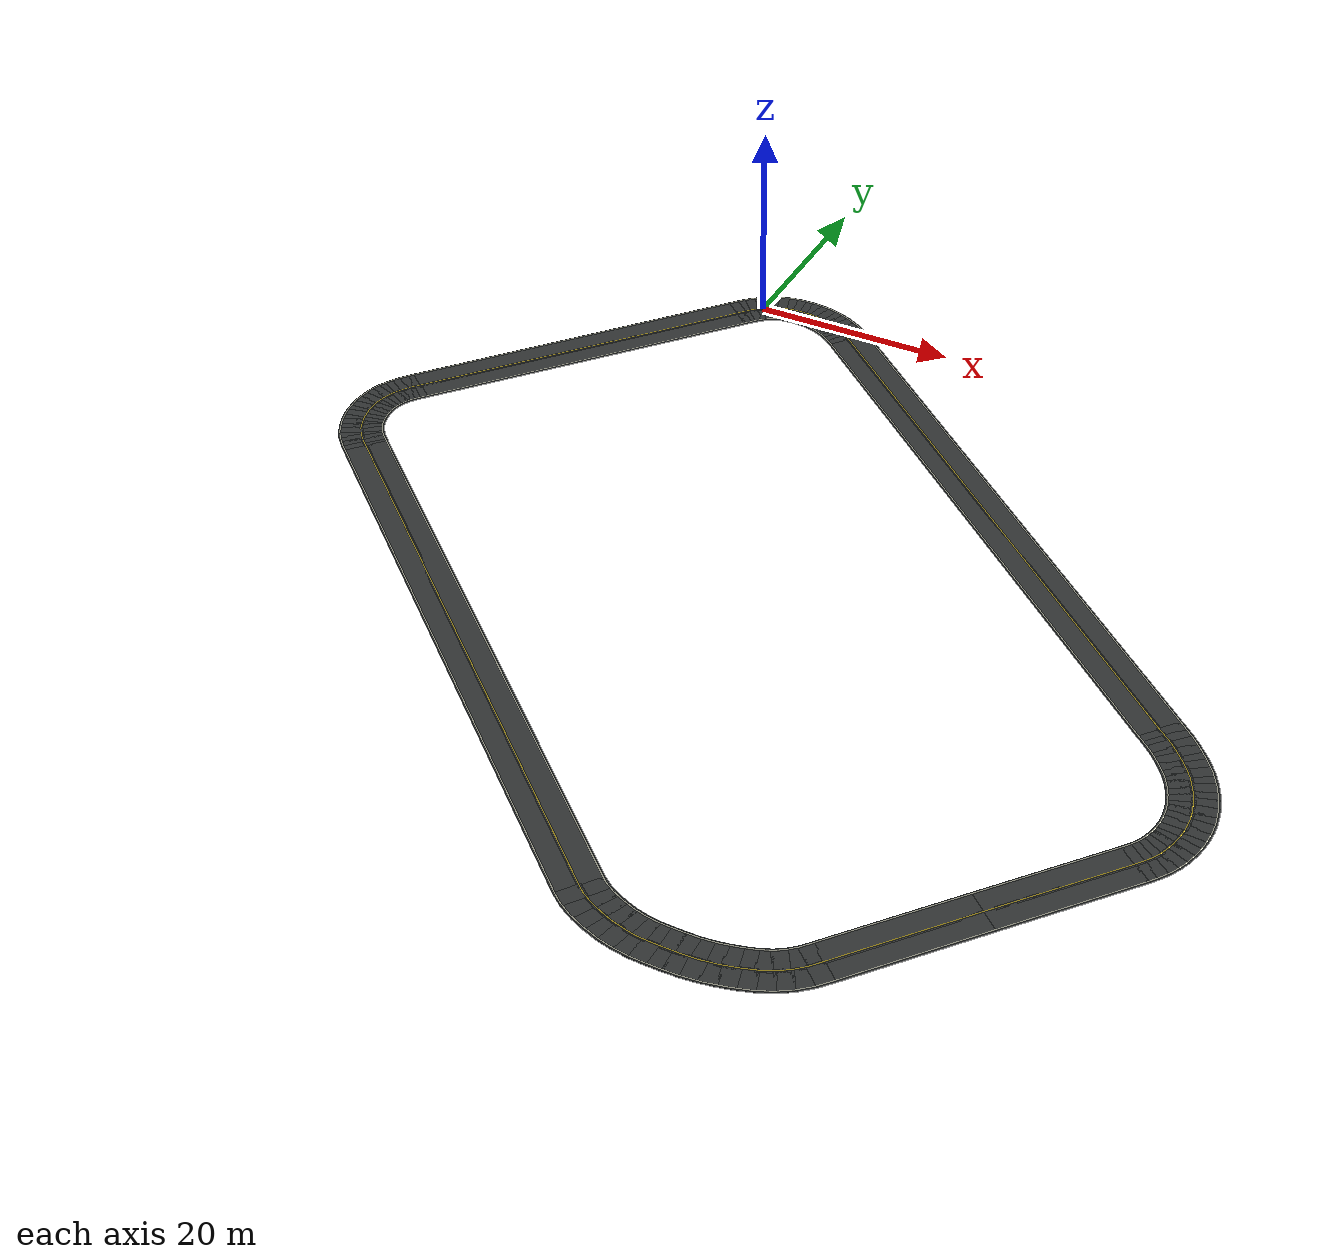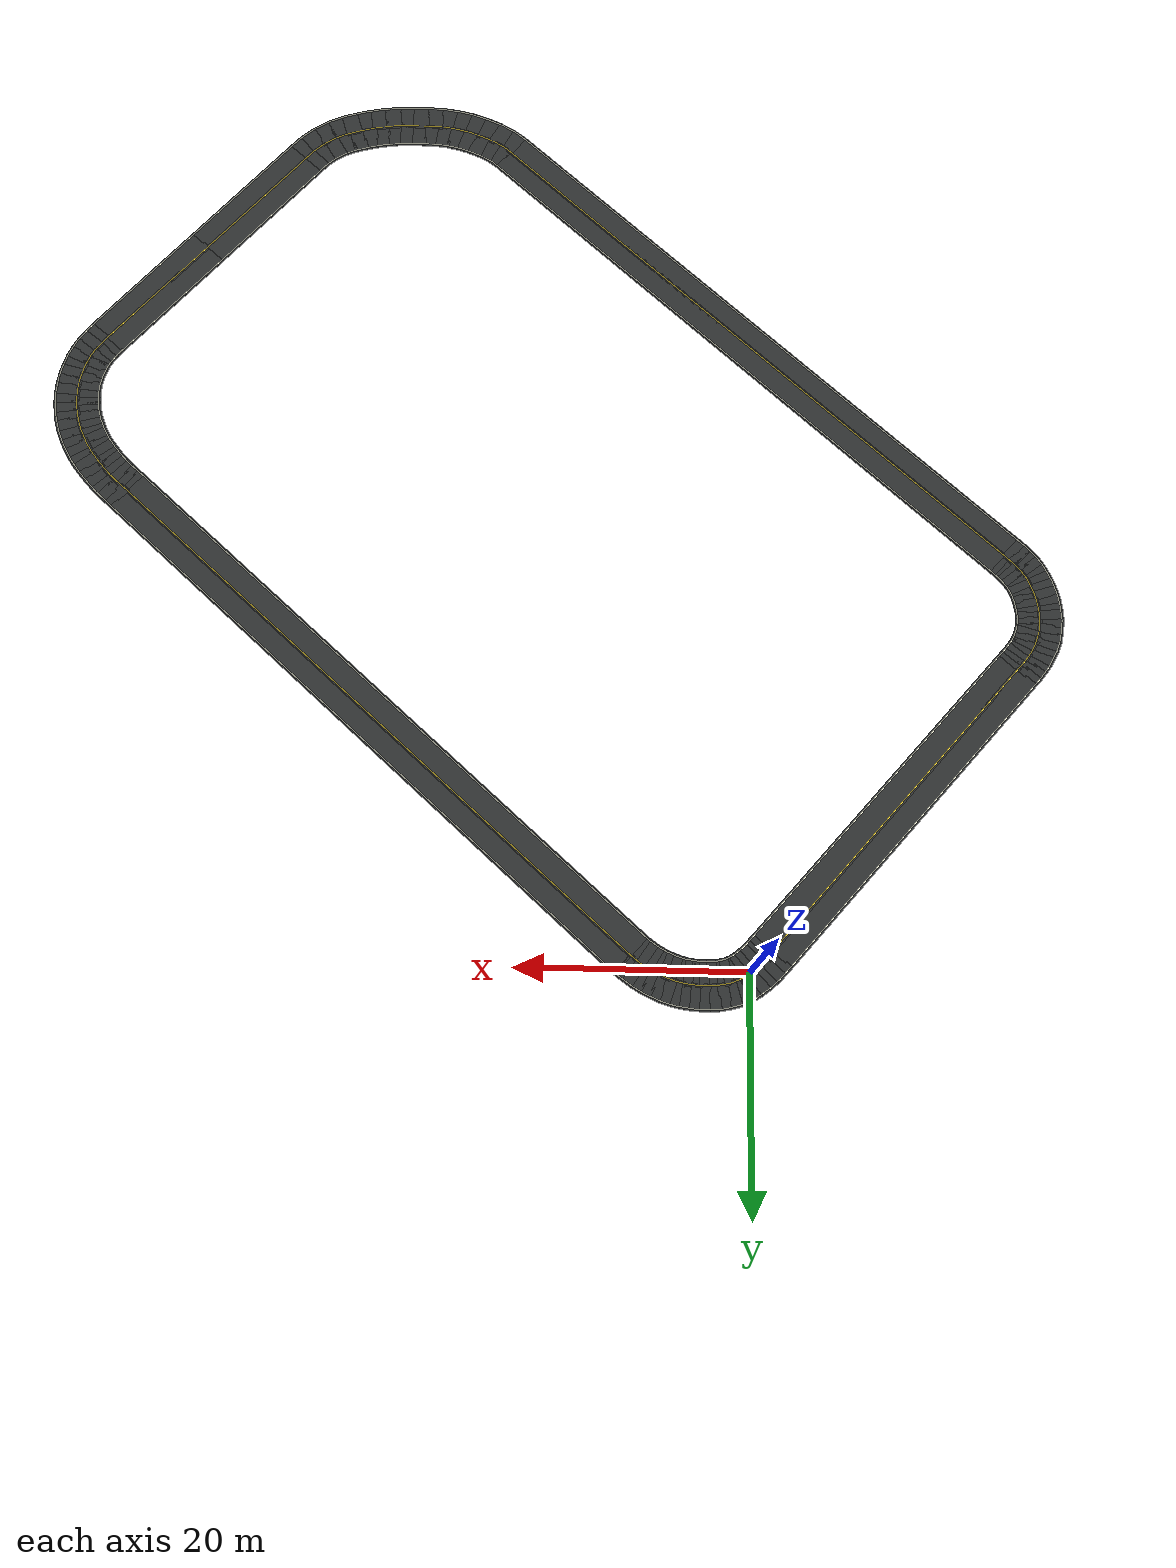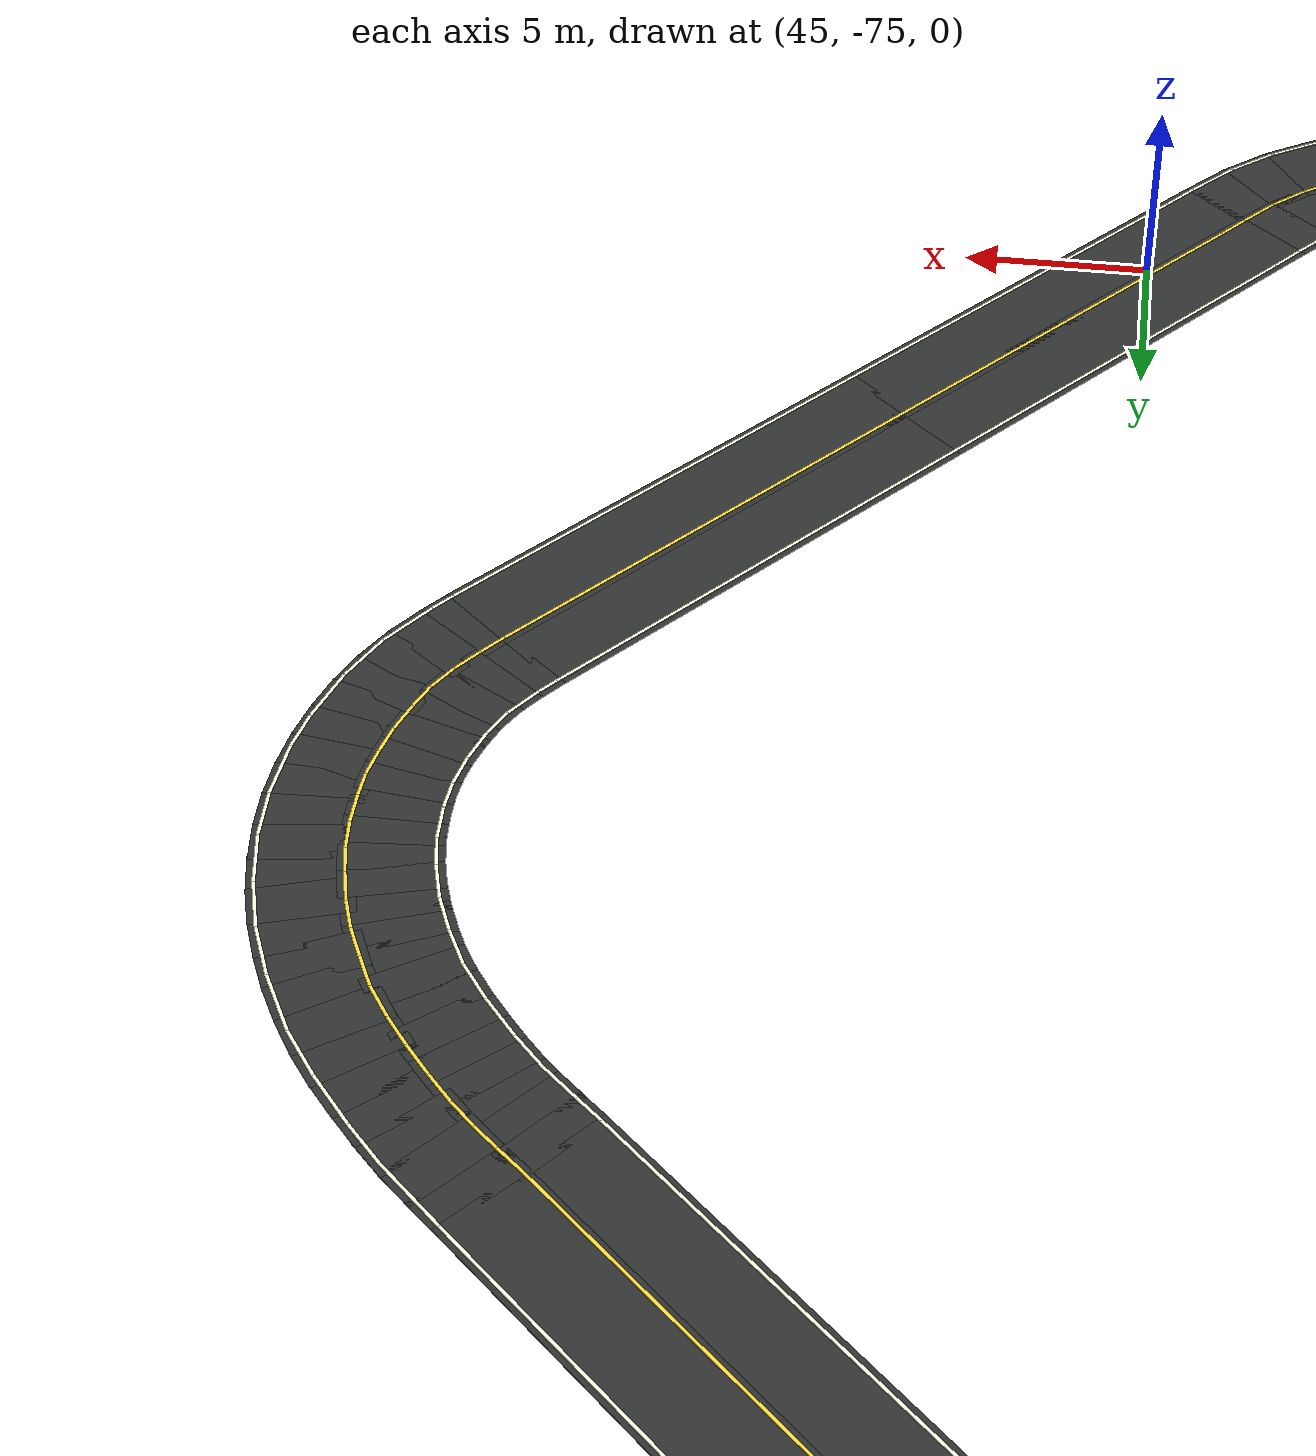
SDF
<?xml version="1.0"?>
<sdf version="1.9">
  <model name="changxing_site">
    <static>true</static>
    <link name="map_link">
    <visual name="lanelet_7_0_visual">
      <pose>0.0674 -57.6716 0.005 0 0 -0.7297</pose>
      <geometry>
        <box>
          <size>61.6108 2.35 0.02</size>
        </box>
      </geometry>
      <material>
        <ambient>0.16 0.17 0.17 1</ambient>
        <diffuse>0.18 0.19 0.19 1</diffuse>
      </material>
    </visual>
    <visual name="lanelet_64_0_visual">
      <pose>23.4381 -78.5015 0.005 0 0 -0.6377</pose>
      <geometry>
        <box>
          <size>1.3664 2.3604 0.02</size>
        </box>
      </geometry>
      <material>
        <ambient>0.16 0.17 0.17 1</ambient>
        <diffuse>0.18 0.19 0.19 1</diffuse>
      </material>
    </visual>
    <visual name="lanelet_64_1_visual">
      <pose>24.4411 -79.1305 0.005 0 0 -0.4825</pose>
      <geometry>
        <box>
          <size>1.3686 2.3688 0.02</size>
        </box>
      </geometry>
      <material>
        <ambient>0.16 0.17 0.17 1</ambient>
        <diffuse>0.18 0.19 0.19 1</diffuse>
      </material>
    </visual>
    <visual name="lanelet_64_2_visual">
      <pose>25.517 -79.6346 0.005 0 0 -0.3938</pose>
      <geometry>
        <box>
          <size>1.37 2.3667 0.02</size>
        </box>
      </geometry>
      <material>
        <ambient>0.16 0.17 0.17 1</ambient>
        <diffuse>0.18 0.19 0.19 1</diffuse>
      </material>
    </visual>
    <visual name="lanelet_64_3_visual">
      <pose>26.6321 -80.0454 0.005 0 0 -0.3121</pose>
      <geometry>
        <box>
          <size>1.3686 2.3657 0.02</size>
        </box>
      </geometry>
      <material>
        <ambient>0.16 0.17 0.17 1</ambient>
        <diffuse>0.18 0.19 0.19 1</diffuse>
      </material>
    </visual>
    <visual name="lanelet_64_4_visual">
      <pose>27.7784 -80.3573 0.005 0 0 -0.2192</pose>
      <geometry>
        <box>
          <size>1.3699 2.37 0.02</size>
        </box>
      </geometry>
      <material>
        <ambient>0.16 0.17 0.17 1</ambient>
        <diffuse>0.18 0.19 0.19 1</diffuse>
      </material>
    </visual>
    <visual name="lanelet_64_5_visual">
      <pose>28.9487 -80.5584 0.005 0 0 -0.121</pose>
      <geometry>
        <box>
          <size>1.3678 2.3724 0.02</size>
        </box>
      </geometry>
      <material>
        <ambient>0.16 0.17 0.17 1</ambient>
        <diffuse>0.18 0.19 0.19 1</diffuse>
      </material>
    </visual>
    <visual name="lanelet_64_6_visual">
      <pose>30.1331 -80.6505 0.005 0 0 -0.0343</pose>
      <geometry>
        <box>
          <size>1.3704 2.3627 0.02</size>
        </box>
      </geometry>
      <material>
        <ambient>0.16 0.17 0.17 1</ambient>
        <diffuse>0.18 0.19 0.19 1</diffuse>
      </material>
    </visual>
    <visual name="lanelet_64_7_visual">
      <pose>31.3232 -80.6751 0.005 0 0 -0.007</pose>
      <geometry>
        <box>
          <size>1.3705 2.3548 0.02</size>
        </box>
      </geometry>
      <material>
        <ambient>0.16 0.17 0.17 1</ambient>
        <diffuse>0.18 0.19 0.19 1</diffuse>
      </material>
    </visual>
    <visual name="lanelet_64_8_visual">
      <pose>32.5135 -80.6675 0.005 0 0 0.0197</pose>
      <geometry>
        <box>
          <size>1.3704 2.3538 0.02</size>
        </box>
      </geometry>
      <material>
        <ambient>0.16 0.17 0.17 1</ambient>
        <diffuse>0.18 0.19 0.19 1</diffuse>
      </material>
    </visual>
    <visual name="lanelet_64_9_visual">
      <pose>33.7006 -80.5983 0.005 0 0 0.0968</pose>
      <geometry>
        <box>
          <size>1.3695 2.3633 0.02</size>
        </box>
      </geometry>
      <material>
        <ambient>0.16 0.17 0.17 1</ambient>
        <diffuse>0.18 0.19 0.19 1</diffuse>
      </material>
    </visual>
    <visual name="lanelet_64_10_visual">
      <pose>34.8797 -80.4457 0.005 0 0 0.1606</pose>
      <geometry>
        <box>
          <size>1.3696 2.3798 0.02</size>
        </box>
      </geometry>
      <material>
        <ambient>0.16 0.17 0.17 1</ambient>
        <diffuse>0.18 0.19 0.19 1</diffuse>
      </material>
    </visual>
    <visual name="lanelet_64_11_visual">
      <pose>36.0464 -80.2153 0.005 0 0 0.2293</pose>
      <geometry>
        <box>
          <size>1.3703 2.3797 0.02</size>
        </box>
      </geometry>
      <material>
        <ambient>0.16 0.17 0.17 1</ambient>
        <diffuse>0.18 0.19 0.19 1</diffuse>
      </material>
    </visual>
    <visual name="lanelet_64_12_visual">
      <pose>37.1963 -79.9099 0.005 0 0 0.29</pose>
      <geometry>
        <box>
          <size>1.3704 2.3763 0.02</size>
        </box>
      </geometry>
      <material>
        <ambient>0.16 0.17 0.17 1</ambient>
        <diffuse>0.18 0.19 0.19 1</diffuse>
      </material>
    </visual>
    <visual name="lanelet_64_13_visual">
      <pose>38.3179 -79.5171 0.005 0 0 0.3838</pose>
      <geometry>
        <box>
          <size>1.3688 2.3755 0.02</size>
        </box>
      </geometry>
      <material>
        <ambient>0.16 0.17 0.17 1</ambient>
        <diffuse>0.18 0.19 0.19 1</diffuse>
      </material>
    </visual>
    <visual name="lanelet_64_14_visual">
      <pose>39.3775 -78.9879 0.005 0 0 0.5427</pose>
      <geometry>
        <box>
          <size>1.3677 2.3623 0.02</size>
        </box>
      </geometry>
      <material>
        <ambient>0.16 0.17 0.17 1</ambient>
        <diffuse>0.18 0.19 0.19 1</diffuse>
      </material>
    </visual>
    <visual name="lanelet_64_15_visual">
      <pose>40.3433 -78.301 0.005 0 0 0.6936</pose>
      <geometry>
        <box>
          <size>1.3693 2.353 0.02</size>
        </box>
      </geometry>
      <material>
        <ambient>0.16 0.17 0.17 1</ambient>
        <diffuse>0.18 0.19 0.19 1</diffuse>
      </material>
    </visual>
    <visual name="lanelet_64_16_visual">
      <pose>41.1997 -77.4794 0.005 0 0 0.8358</pose>
      <geometry>
        <box>
          <size>1.3702 2.3503 0.02</size>
        </box>
      </geometry>
      <material>
        <ambient>0.16 0.17 0.17 1</ambient>
        <diffuse>0.18 0.19 0.19 1</diffuse>
      </material>
    </visual>
    <visual name="lanelet_68_0_visual">
      <pose>-1.2659 -59.1623 0.005 0 0 -0.7297</pose>
      <geometry>
        <box>
          <size>61.6108 2.35 0.02</size>
        </box>
      </geometry>
      <material>
        <ambient>0.16 0.17 0.17 1</ambient>
        <diffuse>0.18 0.19 0.19 1</diffuse>
      </material>
    </visual>
    <visual name="lanelet_86_0_visual">
      <pose>22.1735 -80.0546 0.005 0 0 -0.6511</pose>
      <geometry>
        <box>
          <size>1.5512 2.3495 0.02</size>
        </box>
      </geometry>
      <material>
        <ambient>0.16 0.17 0.17 1</ambient>
        <diffuse>0.18 0.19 0.19 1</diffuse>
      </material>
    </visual>
    <visual name="lanelet_86_1_visual">
      <pose>23.3199 -80.8012 0.005 0 0 -0.5034</pose>
      <geometry>
        <box>
          <size>1.5525 2.3595 0.02</size>
        </box>
      </geometry>
      <material>
        <ambient>0.16 0.17 0.17 1</ambient>
        <diffuse>0.18 0.19 0.19 1</diffuse>
      </material>
    </visual>
    <visual name="lanelet_86_2_visual">
      <pose>24.5536 -81.4002 0.005 0 0 -0.4007</pose>
      <geometry>
        <box>
          <size>1.554 2.3602 0.02</size>
        </box>
      </geometry>
      <material>
        <ambient>0.16 0.17 0.17 1</ambient>
        <diffuse>0.18 0.19 0.19 1</diffuse>
      </material>
    </visual>
    <visual name="lanelet_86_3_visual">
      <pose>25.8362 -81.8893 0.005 0 0 -0.3279</pose>
      <geometry>
        <box>
          <size>1.5533 2.3553 0.02</size>
        </box>
      </geometry>
      <material>
        <ambient>0.16 0.17 0.17 1</ambient>
        <diffuse>0.18 0.19 0.19 1</diffuse>
      </material>
    </visual>
    <visual name="lanelet_86_4_visual">
      <pose>27.1553 -82.2663 0.005 0 0 -0.2289</pose>
      <geometry>
        <box>
          <size>1.5539 2.3505 0.02</size>
        </box>
      </geometry>
      <material>
        <ambient>0.16 0.17 0.17 1</ambient>
        <diffuse>0.18 0.19 0.19 1</diffuse>
      </material>
    </visual>
    <visual name="lanelet_86_5_visual">
      <pose>28.5041 -82.5166 0.005 0 0 -0.138</pose>
      <geometry>
        <box>
          <size>1.5525 2.3479 0.02</size>
        </box>
      </geometry>
      <material>
        <ambient>0.16 0.17 0.17 1</ambient>
        <diffuse>0.18 0.19 0.19 1</diffuse>
      </material>
    </visual>
    <visual name="lanelet_86_6_visual">
      <pose>29.8702 -82.6395 0.005 0 0 -0.0415</pose>
      <geometry>
        <box>
          <size>1.554 2.3541 0.02</size>
        </box>
      </geometry>
      <material>
        <ambient>0.16 0.17 0.17 1</ambient>
        <diffuse>0.18 0.19 0.19 1</diffuse>
      </material>
    </visual>
    <visual name="lanelet_86_7_visual">
      <pose>31.2438 -82.6729 0.005 0 0 -0.0071</pose>
      <geometry>
        <box>
          <size>1.5544 2.3482 0.02</size>
        </box>
      </geometry>
      <material>
        <ambient>0.16 0.17 0.17 1</ambient>
        <diffuse>0.18 0.19 0.19 1</diffuse>
      </material>
    </visual>
    <visual name="lanelet_86_8_visual">
      <pose>32.6177 -82.6603 0.005 0 0 0.0254</pose>
      <geometry>
        <box>
          <size>1.554 2.3415 0.02</size>
        </box>
      </geometry>
      <material>
        <ambient>0.16 0.17 0.17 1</ambient>
        <diffuse>0.18 0.19 0.19 1</diffuse>
      </material>
    </visual>
    <visual name="lanelet_86_9_visual">
      <pose>33.9879 -82.5758 0.005 0 0 0.0979</pose>
      <geometry>
        <box>
          <size>1.5535 2.3374 0.02</size>
        </box>
      </geometry>
      <material>
        <ambient>0.16 0.17 0.17 1</ambient>
        <diffuse>0.18 0.19 0.19 1</diffuse>
      </material>
    </visual>
    <visual name="lanelet_86_10_visual">
      <pose>35.3479 -82.3914 0.005 0 0 0.1716</pose>
      <geometry>
        <box>
          <size>1.5534 2.327 0.02</size>
        </box>
      </geometry>
      <material>
        <ambient>0.16 0.17 0.17 1</ambient>
        <diffuse>0.18 0.19 0.19 1</diffuse>
      </material>
    </visual>
    <visual name="lanelet_86_11_visual">
      <pose>36.6918 -82.1108 0.005 0 0 0.2402</pose>
      <geometry>
        <box>
          <size>1.5539 2.3291 0.02</size>
        </box>
      </geometry>
      <material>
        <ambient>0.16 0.17 0.17 1</ambient>
        <diffuse>0.18 0.19 0.19 1</diffuse>
      </material>
    </visual>
    <visual name="lanelet_86_12_visual">
      <pose>38.0141 -81.7413 0.005 0 0 0.3047</pose>
      <geometry>
        <box>
          <size>1.5535 2.3393 0.02</size>
        </box>
      </geometry>
      <material>
        <ambient>0.16 0.17 0.17 1</ambient>
        <diffuse>0.18 0.19 0.19 1</diffuse>
      </material>
    </visual>
    <visual name="lanelet_86_13_visual">
      <pose>39.2993 -81.2643 0.005 0 0 0.4062</pose>
      <geometry>
        <box>
          <size>1.5519 2.3366 0.02</size>
        </box>
      </geometry>
      <material>
        <ambient>0.16 0.17 0.17 1</ambient>
        <diffuse>0.18 0.19 0.19 1</diffuse>
      </material>
    </visual>
    <visual name="lanelet_86_14_visual">
      <pose>40.5123 -80.6313 0.005 0 0 0.5557</pose>
      <geometry>
        <box>
          <size>1.5524 2.3362 0.02</size>
        </box>
      </geometry>
      <material>
        <ambient>0.16 0.17 0.17 1</ambient>
        <diffuse>0.18 0.19 0.19 1</diffuse>
      </material>
    </visual>
    <visual name="lanelet_86_15_visual">
      <pose>41.6221 -79.829 0.005 0 0 0.6962</pose>
      <geometry>
        <box>
          <size>1.5531 2.3361 0.02</size>
        </box>
      </geometry>
      <material>
        <ambient>0.16 0.17 0.17 1</ambient>
        <diffuse>0.18 0.19 0.19 1</diffuse>
      </material>
    </visual>
    <visual name="lanelet_86_16_visual">
      <pose>42.6151 -78.8841 0.005 0 0 0.825</pose>
      <geometry>
        <box>
          <size>1.554 2.3422 0.02</size>
        </box>
      </geometry>
      <material>
        <ambient>0.16 0.17 0.17 1</ambient>
        <diffuse>0.18 0.19 0.19 1</diffuse>
      </material>
    </visual>
    <visual name="lanelet_93_0_visual">
      <pose>45.9396 -72.115 0.005 0 0 0.8482</pose>
      <geometry>
        <box>
          <size>13.3067 2.3486 0.02</size>
        </box>
      </geometry>
      <material>
        <ambient>0.16 0.17 0.17 1</ambient>
        <diffuse>0.18 0.19 0.19 1</diffuse>
      </material>
    </visual>
    <visual name="lanelet_93_1_visual">
      <pose>54.6263 -62.2737 0.005 0 0 0.8471</pose>
      <geometry>
        <box>
          <size>13.3068 2.3489 0.02</size>
        </box>
      </geometry>
      <material>
        <ambient>0.16 0.17 0.17 1</ambient>
        <diffuse>0.18 0.19 0.19 1</diffuse>
      </material>
    </visual>
    <visual name="lanelet_97_0_visual">
      <pose>47.4258 -73.4519 0.005 0 0 0.8482</pose>
      <geometry>
        <box>
          <size>13.3186 2.3496 0.02</size>
        </box>
      </geometry>
      <material>
        <ambient>0.16 0.17 0.17 1</ambient>
        <diffuse>0.18 0.19 0.19 1</diffuse>
      </material>
    </visual>
    <visual name="lanelet_97_1_visual">
      <pose>56.1204 -63.6017 0.005 0 0 0.8471</pose>
      <geometry>
        <box>
          <size>13.3187 2.3491 0.02</size>
        </box>
      </geometry>
      <material>
        <ambient>0.16 0.17 0.17 1</ambient>
        <diffuse>0.18 0.19 0.19 1</diffuse>
      </material>
    </visual>
    <visual name="lanelet_188_0_visual">
      <pose>59.2116 -57.0662 0.005 0 0 0.8792</pose>
      <geometry>
        <box>
          <size>0.9305 2.3499 0.02</size>
        </box>
      </geometry>
      <material>
        <ambient>0.16 0.17 0.17 1</ambient>
        <diffuse>0.18 0.19 0.19 1</diffuse>
      </material>
    </visual>
    <visual name="lanelet_188_1_visual">
      <pose>59.6759 -56.4769 0.005 0 0 0.9278</pose>
      <geometry>
        <box>
          <size>0.9304 2.3579 0.02</size>
        </box>
      </geometry>
      <material>
        <ambient>0.16 0.17 0.17 1</ambient>
        <diffuse>0.18 0.19 0.19 1</diffuse>
      </material>
    </visual>
    <visual name="lanelet_188_2_visual">
      <pose>60.0869 -55.8517 0.005 0 0 1.0507</pose>
      <geometry>
        <box>
          <size>0.9289 2.3732 0.02</size>
        </box>
      </geometry>
      <material>
        <ambient>0.16 0.17 0.17 1</ambient>
        <diffuse>0.18 0.19 0.19 1</diffuse>
      </material>
    </visual>
    <visual name="lanelet_188_3_visual">
      <pose>60.411 -55.1782 0.005 0 0 1.1939</pose>
      <geometry>
        <box>
          <size>0.9298 2.374 0.02</size>
        </box>
      </geometry>
      <material>
        <ambient>0.16 0.17 0.17 1</ambient>
        <diffuse>0.18 0.19 0.19 1</diffuse>
      </material>
    </visual>
    <visual name="lanelet_188_4_visual">
      <pose>60.6621 -54.4721 0.005 0 0 1.2643</pose>
      <geometry>
        <box>
          <size>0.9299 2.3672 0.02</size>
        </box>
      </geometry>
      <material>
        <ambient>0.16 0.17 0.17 1</ambient>
        <diffuse>0.18 0.19 0.19 1</diffuse>
      </material>
    </visual>
    <visual name="lanelet_188_5_visual">
      <pose>60.8548 -53.7479 0.005 0 0 1.3573</pose>
      <geometry>
        <box>
          <size>0.9305 2.3641 0.02</size>
        </box>
      </geometry>
      <material>
        <ambient>0.16 0.17 0.17 1</ambient>
        <diffuse>0.18 0.19 0.19 1</diffuse>
      </material>
    </visual>
    <visual name="lanelet_188_6_visual">
      <pose>60.9755 -53.0088 0.005 0 0 1.4607</pose>
      <geometry>
        <box>
          <size>0.9293 2.3738 0.02</size>
        </box>
      </geometry>
      <material>
        <ambient>0.16 0.17 0.17 1</ambient>
        <diffuse>0.18 0.19 0.19 1</diffuse>
      </material>
    </visual>
    <visual name="lanelet_188_7_visual">
      <pose>61.0168 -52.2614 0.005 0 0 1.5703</pose>
      <geometry>
        <box>
          <size>0.93 2.3906 0.02</size>
        </box>
      </geometry>
      <material>
        <ambient>0.16 0.17 0.17 1</ambient>
        <diffuse>0.18 0.19 0.19 1</diffuse>
      </material>
    </visual>
    <visual name="lanelet_188_8_visual">
      <pose>60.9897 -51.5128 0.005 0 0 1.6438</pose>
      <geometry>
        <box>
          <size>0.9293 2.3985 0.02</size>
        </box>
      </geometry>
      <material>
        <ambient>0.16 0.17 0.17 1</ambient>
        <diffuse>0.18 0.19 0.19 1</diffuse>
      </material>
    </visual>
    <visual name="lanelet_188_9_visual">
      <pose>60.8982 -50.7699 0.005 0 0 1.7429</pose>
      <geometry>
        <box>
          <size>0.9296 2.405 0.02</size>
        </box>
      </geometry>
      <material>
        <ambient>0.16 0.17 0.17 1</ambient>
        <diffuse>0.18 0.19 0.19 1</diffuse>
      </material>
    </visual>
    <visual name="lanelet_188_10_visual">
      <pose>60.7394 -50.0376 0.005 0 0 1.8258</pose>
      <geometry>
        <box>
          <size>0.9304 2.4061 0.02</size>
        </box>
      </geometry>
      <material>
        <ambient>0.16 0.17 0.17 1</ambient>
        <diffuse>0.18 0.19 0.19 1</diffuse>
      </material>
    </visual>
    <visual name="lanelet_188_11_visual">
      <pose>60.5213 -49.3208 0.005 0 0 1.9065</pose>
      <geometry>
        <box>
          <size>0.9291 2.4168 0.02</size>
        </box>
      </geometry>
      <material>
        <ambient>0.16 0.17 0.17 1</ambient>
        <diffuse>0.18 0.19 0.19 1</diffuse>
      </material>
    </visual>
    <visual name="lanelet_188_12_visual">
      <pose>60.2463 -48.6244 0.005 0 0 1.9871</pose>
      <geometry>
        <box>
          <size>0.9297 2.4236 0.02</size>
        </box>
      </geometry>
      <material>
        <ambient>0.16 0.17 0.17 1</ambient>
        <diffuse>0.18 0.19 0.19 1</diffuse>
      </material>
    </visual>
    <visual name="lanelet_188_13_visual">
      <pose>59.9235 -47.9476 0.005 0 0 2.0446</pose>
      <geometry>
        <box>
          <size>0.9306 2.4144 0.02</size>
        </box>
      </geometry>
      <material>
        <ambient>0.16 0.17 0.17 1</ambient>
        <diffuse>0.18 0.19 0.19 1</diffuse>
      </material>
    </visual>
    <visual name="lanelet_188_14_visual">
      <pose>59.5539 -47.2963 0.005 0 0 2.1293</pose>
      <geometry>
        <box>
          <size>0.9284 2.4209 0.02</size>
        </box>
      </geometry>
      <material>
        <ambient>0.16 0.17 0.17 1</ambient>
        <diffuse>0.18 0.19 0.19 1</diffuse>
      </material>
    </visual>
    <visual name="lanelet_188_15_visual">
      <pose>59.1336 -46.6765 0.005 0 0 2.204</pose>
      <geometry>
        <box>
          <size>0.9304 2.4239 0.02</size>
        </box>
      </geometry>
      <material>
        <ambient>0.16 0.17 0.17 1</ambient>
        <diffuse>0.18 0.19 0.19 1</diffuse>
      </material>
    </visual>
    <visual name="lanelet_188_16_visual">
      <pose>58.6724 -46.085 0.005 0 0 2.2622</pose>
      <geometry>
        <box>
          <size>0.9305 2.4112 0.02</size>
        </box>
      </geometry>
      <material>
        <ambient>0.16 0.17 0.17 1</ambient>
        <diffuse>0.18 0.19 0.19 1</diffuse>
      </material>
    </visual>
    <visual name="lanelet_188_17_visual">
      <pose>58.1853 -45.5141 0.005 0 0 2.292</pose>
      <geometry>
        <box>
          <size>0.9305 2.398 0.02</size>
        </box>
      </geometry>
      <material>
        <ambient>0.16 0.17 0.17 1</ambient>
        <diffuse>0.18 0.19 0.19 1</diffuse>
      </material>
    </visual>
    <visual name="lanelet_188_18_visual">
      <pose>57.6798 -44.9595 0.005 0 0 2.3278</pose>
      <geometry>
        <box>
          <size>0.9306 2.386 0.02</size>
        </box>
      </geometry>
      <material>
        <ambient>0.16 0.17 0.17 1</ambient>
        <diffuse>0.18 0.19 0.19 1</diffuse>
      </material>
    </visual>
    <visual name="lanelet_188_19_visual">
      <pose>57.148 -44.4305 0.005 0 0 2.3901</pose>
      <geometry>
        <box>
          <size>0.9303 2.3833 0.02</size>
        </box>
      </geometry>
      <material>
        <ambient>0.16 0.17 0.17 1</ambient>
        <diffuse>0.18 0.19 0.19 1</diffuse>
      </material>
    </visual>
    <visual name="lanelet_188_20_visual">
      <pose>56.59 -43.9289 0.005 0 0 2.4287</pose>
      <geometry>
        <box>
          <size>0.9306 2.3751 0.02</size>
        </box>
      </geometry>
      <material>
        <ambient>0.16 0.17 0.17 1</ambient>
        <diffuse>0.18 0.19 0.19 1</diffuse>
      </material>
    </visual>
    <visual name="lanelet_188_21_visual">
      <pose>56.0186 -43.4421 0.005 0 0 2.4432</pose>
      <geometry>
        <box>
          <size>0.9307 2.3581 0.02</size>
        </box>
      </geometry>
      <material>
        <ambient>0.16 0.17 0.17 1</ambient>
        <diffuse>0.18 0.19 0.19 1</diffuse>
      </material>
    </visual>
    <visual name="lanelet_205_0_visual">
      <pose>60.7521 -58.3335 0.005 0 0 0.8868</pose>
      <geometry>
        <box>
          <size>1.0715 2.3421 0.02</size>
        </box>
      </geometry>
      <material>
        <ambient>0.16 0.17 0.17 1</ambient>
        <diffuse>0.18 0.19 0.19 1</diffuse>
      </material>
    </visual>
    <visual name="lanelet_205_1_visual">
      <pose>61.3004 -57.6307 0.005 0 0 0.9297</pose>
      <geometry>
        <box>
          <size>1.0715 2.3296 0.02</size>
        </box>
      </geometry>
      <material>
        <ambient>0.16 0.17 0.17 1</ambient>
        <diffuse>0.18 0.19 0.19 1</diffuse>
      </material>
    </visual>
    <visual name="lanelet_205_2_visual">
      <pose>61.7894 -56.8882 0.005 0 0 1.0471</pose>
      <geometry>
        <box>
          <size>1.0696 2.3156 0.02</size>
        </box>
      </geometry>
      <material>
        <ambient>0.16 0.17 0.17 1</ambient>
        <diffuse>0.18 0.19 0.19 1</diffuse>
      </material>
    </visual>
    <visual name="lanelet_205_3_visual">
      <pose>62.1883 -56.0942 0.005 0 0 1.1633</pose>
      <geometry>
        <box>
          <size>1.0706 2.3275 0.02</size>
        </box>
      </geometry>
      <material>
        <ambient>0.16 0.17 0.17 1</ambient>
        <diffuse>0.18 0.19 0.19 1</diffuse>
      </material>
    </visual>
    <visual name="lanelet_205_4_visual">
      <pose>62.5032 -55.2617 0.005 0 0 1.2551</pose>
      <geometry>
        <box>
          <size>1.0714 2.3418 0.02</size>
        </box>
      </geometry>
      <material>
        <ambient>0.16 0.17 0.17 1</ambient>
        <diffuse>0.18 0.19 0.19 1</diffuse>
      </material>
    </visual>
    <visual name="lanelet_205_5_visual">
      <pose>62.7461 -54.405 0.005 0 0 1.3339</pose>
      <geometry>
        <box>
          <size>1.0709 2.3429 0.02</size>
        </box>
      </geometry>
      <material>
        <ambient>0.16 0.17 0.17 1</ambient>
        <diffuse>0.18 0.19 0.19 1</diffuse>
      </material>
    </visual>
    <visual name="lanelet_205_6_visual">
      <pose>62.9139 -53.5315 0.005 0 0 1.4281</pose>
      <geometry>
        <box>
          <size>1.07 2.3442 0.02</size>
        </box>
      </geometry>
      <material>
        <ambient>0.16 0.17 0.17 1</ambient>
        <diffuse>0.18 0.19 0.19 1</diffuse>
      </material>
    </visual>
    <visual name="lanelet_205_7_visual">
      <pose>63.0002 -52.646 0.005 0 0 1.5193</pose>
      <geometry>
        <box>
          <size>1.0713 2.3526 0.02</size>
        </box>
      </geometry>
      <material>
        <ambient>0.16 0.17 0.17 1</ambient>
        <diffuse>0.18 0.19 0.19 1</diffuse>
      </material>
    </visual>
    <visual name="lanelet_205_8_visual">
      <pose>63.0051 -51.7559 0.005 0 0 1.6112</pose>
      <geometry>
        <box>
          <size>1.0709 2.3642 0.02</size>
        </box>
      </geometry>
      <material>
        <ambient>0.16 0.17 0.17 1</ambient>
        <diffuse>0.18 0.19 0.19 1</diffuse>
      </material>
    </visual>
    <visual name="lanelet_205_9_visual">
      <pose>62.9289 -50.8696 0.005 0 0 1.702</pose>
      <geometry>
        <box>
          <size>1.07 2.364 0.02</size>
        </box>
      </geometry>
      <material>
        <ambient>0.16 0.17 0.17 1</ambient>
        <diffuse>0.18 0.19 0.19 1</diffuse>
      </material>
    </visual>
    <visual name="lanelet_205_10_visual">
      <pose>62.7798 -49.9921 0.005 0 0 1.7763</pose>
      <geometry>
        <box>
          <size>1.0713 2.3784 0.02</size>
        </box>
      </geometry>
      <material>
        <ambient>0.16 0.17 0.17 1</ambient>
        <diffuse>0.18 0.19 0.19 1</diffuse>
      </material>
    </visual>
    <visual name="lanelet_205_11_visual">
      <pose>62.561 -49.1289 0.005 0 0 1.8619</pose>
      <geometry>
        <box>
          <size>1.0714 2.3833 0.02</size>
        </box>
      </geometry>
      <material>
        <ambient>0.16 0.17 0.17 1</ambient>
        <diffuse>0.18 0.19 0.19 1</diffuse>
      </material>
    </visual>
    <visual name="lanelet_205_12_visual">
      <pose>62.2685 -48.2885 0.005 0 0 1.9496</pose>
      <geometry>
        <box>
          <size>1.0701 2.3788 0.02</size>
        </box>
      </geometry>
      <material>
        <ambient>0.16 0.17 0.17 1</ambient>
        <diffuse>0.18 0.19 0.19 1</diffuse>
      </material>
    </visual>
    <visual name="lanelet_205_13_visual">
      <pose>61.9145 -47.4715 0.005 0 0 2.0098</pose>
      <geometry>
        <box>
          <size>1.0713 2.3824 0.02</size>
        </box>
      </geometry>
      <material>
        <ambient>0.16 0.17 0.17 1</ambient>
        <diffuse>0.18 0.19 0.19 1</diffuse>
      </material>
    </visual>
    <visual name="lanelet_205_14_visual">
      <pose>61.506 -46.6803 0.005 0 0 2.0849</pose>
      <geometry>
        <box>
          <size>1.0708 2.3759 0.02</size>
        </box>
      </geometry>
      <material>
        <ambient>0.16 0.17 0.17 1</ambient>
        <diffuse>0.18 0.19 0.19 1</diffuse>
      </material>
    </visual>
    <visual name="lanelet_205_15_visual">
      <pose>61.04 -45.9222 0.005 0 0 2.159</pose>
      <geometry>
        <box>
          <size>1.0702 2.3793 0.02</size>
        </box>
      </geometry>
      <material>
        <ambient>0.16 0.17 0.17 1</ambient>
        <diffuse>0.18 0.19 0.19 1</diffuse>
      </material>
    </visual>
    <visual name="lanelet_205_16_visual">
      <pose>60.5211 -45.1986 0.005 0 0 2.2269</pose>
      <geometry>
        <box>
          <size>1.0716 2.392 0.02</size>
        </box>
      </geometry>
      <material>
        <ambient>0.16 0.17 0.17 1</ambient>
        <diffuse>0.18 0.19 0.19 1</diffuse>
      </material>
    </visual>
    <visual name="lanelet_205_17_visual">
      <pose>59.9581 -44.5076 0.005 0 0 2.282</pose>
      <geometry>
        <box>
          <size>1.0718 2.3818 0.02</size>
        </box>
      </geometry>
      <material>
        <ambient>0.16 0.17 0.17 1</ambient>
        <diffuse>0.18 0.19 0.19 1</diffuse>
      </material>
    </visual>
    <visual name="lanelet_205_18_visual">
      <pose>59.3671 -43.84 0.005 0 0 2.3089</pose>
      <geometry>
        <box>
          <size>1.0716 2.3664 0.02</size>
        </box>
      </geometry>
      <material>
        <ambient>0.16 0.17 0.17 1</ambient>
        <diffuse>0.18 0.19 0.19 1</diffuse>
      </material>
    </visual>
    <visual name="lanelet_205_19_visual">
      <pose>58.752 -43.195 0.005 0 0 2.3561</pose>
      <geometry>
        <box>
          <size>1.0715 2.3688 0.02</size>
        </box>
      </geometry>
      <material>
        <ambient>0.16 0.17 0.17 1</ambient>
        <diffuse>0.18 0.19 0.19 1</diffuse>
      </material>
    </visual>
    <visual name="lanelet_205_20_visual">
      <pose>58.1034 -42.5837 0.005 0 0 2.4154</pose>
      <geometry>
        <box>
          <size>1.0717 2.3773 0.02</size>
        </box>
      </geometry>
      <material>
        <ambient>0.16 0.17 0.17 1</ambient>
        <diffuse>0.18 0.19 0.19 1</diffuse>
      </material>
    </visual>
    <visual name="lanelet_205_21_visual">
      <pose>57.4342 -41.9945 0.005 0 0 2.4239</pose>
      <geometry>
        <box>
          <size>1.0716 2.394 0.02</size>
        </box>
      </geometry>
      <material>
        <ambient>0.16 0.17 0.17 1</ambient>
        <diffuse>0.18 0.19 0.19 1</diffuse>
      </material>
    </visual>
    <visual name="lanelet_212_0_visual">
      <pose>32.5279 -22.5912 0.005 0 0 2.4153</pose>
      <geometry>
        <box>
          <size>62.2491 2.35 0.02</size>
        </box>
      </geometry>
      <material>
        <ambient>0.16 0.17 0.17 1</ambient>
        <diffuse>0.18 0.19 0.19 1</diffuse>
      </material>
    </visual>
    <visual name="lanelet_215_0_visual">
      <pose>33.8756 -21.0939 0.005 0 0 2.4158</pose>
      <geometry>
        <box>
          <size>62.2756 2.3793 0.02</size>
        </box>
      </geometry>
      <material>
        <ambient>0.16 0.17 0.17 1</ambient>
        <diffuse>0.18 0.19 0.19 1</diffuse>
      </material>
    </visual>
    <visual name="lanelet_266_0_visual">
      <pose>9.0769 -1.7815 0.005 0 0 2.4618</pose>
      <geometry>
        <box>
          <size>0.8171 2.3507 0.02</size>
        </box>
      </geometry>
      <material>
        <ambient>0.16 0.17 0.17 1</ambient>
        <diffuse>0.18 0.19 0.19 1</diffuse>
      </material>
    </visual>
    <visual name="lanelet_266_1_visual">
      <pose>8.5676 -1.3993 0.005 0 0 2.5338</pose>
      <geometry>
        <box>
          <size>0.8172 2.3576 0.02</size>
        </box>
      </geometry>
      <material>
        <ambient>0.16 0.17 0.17 1</ambient>
        <diffuse>0.18 0.19 0.19 1</diffuse>
      </material>
    </visual>
    <visual name="lanelet_266_2_visual">
      <pose>8.0331 -1.0533 0.005 0 0 2.6004</pose>
      <geometry>
        <box>
          <size>0.8169 2.3644 0.02</size>
        </box>
      </geometry>
      <material>
        <ambient>0.16 0.17 0.17 1</ambient>
        <diffuse>0.18 0.19 0.19 1</diffuse>
      </material>
    </visual>
    <visual name="lanelet_266_3_visual">
      <pose>7.4763 -0.7448 0.005 0 0 2.671</pose>
      <geometry>
        <box>
          <size>0.817 2.3605 0.02</size>
        </box>
      </geometry>
      <material>
        <ambient>0.16 0.17 0.17 1</ambient>
        <diffuse>0.18 0.19 0.19 1</diffuse>
      </material>
    </visual>
    <visual name="lanelet_266_4_visual">
      <pose>6.899 -0.4763 0.005 0 0 2.7414</pose>
      <geometry>
        <box>
          <size>0.8173 2.3612 0.02</size>
        </box>
      </geometry>
      <material>
        <ambient>0.16 0.17 0.17 1</ambient>
        <diffuse>0.18 0.19 0.19 1</diffuse>
      </material>
    </visual>
    <visual name="lanelet_266_5_visual">
      <pose>6.3048 -0.2474 0.005 0 0 2.8065</pose>
      <geometry>
        <box>
          <size>0.8169 2.3704 0.02</size>
        </box>
      </geometry>
      <material>
        <ambient>0.16 0.17 0.17 1</ambient>
        <diffuse>0.18 0.19 0.19 1</diffuse>
      </material>
    </visual>
    <visual name="lanelet_266_6_visual">
      <pose>5.6959 -0.0627 0.005 0 0 2.8877</pose>
      <geometry>
        <box>
          <size>0.8168 2.3681 0.02</size>
        </box>
      </geometry>
      <material>
        <ambient>0.16 0.17 0.17 1</ambient>
        <diffuse>0.18 0.19 0.19 1</diffuse>
      </material>
    </visual>
    <visual name="lanelet_266_7_visual">
      <pose>5.0722 0.0613 0.005 0 0 3.0028</pose>
      <geometry>
        <box>
          <size>0.8171 2.3626 0.02</size>
        </box>
      </geometry>
      <material>
        <ambient>0.16 0.17 0.17 1</ambient>
        <diffuse>0.18 0.19 0.19 1</diffuse>
      </material>
    </visual>
    <visual name="lanelet_266_8_visual">
      <pose>4.4395 0.1318 0.005 0 0 3.0583</pose>
      <geometry>
        <box>
          <size>0.8166 2.3604 0.02</size>
        </box>
      </geometry>
      <material>
        <ambient>0.16 0.17 0.17 1</ambient>
        <diffuse>0.18 0.19 0.19 1</diffuse>
      </material>
    </visual>
    <visual name="lanelet_266_9_visual">
      <pose>3.8039 0.1661 0.005 0 0 3.1171</pose>
      <geometry>
        <box>
          <size>0.8171 2.3612 0.02</size>
        </box>
      </geometry>
      <material>
        <ambient>0.16 0.17 0.17 1</ambient>
        <diffuse>0.18 0.19 0.19 1</diffuse>
      </material>
    </visual>
    <visual name="lanelet_266_10_visual">
      <pose>3.168 0.1546 0.005 0 0 -3.0808</pose>
      <geometry>
        <box>
          <size>0.816 2.3685 0.02</size>
        </box>
      </geometry>
      <material>
        <ambient>0.16 0.17 0.17 1</ambient>
        <diffuse>0.18 0.19 0.19 1</diffuse>
      </material>
    </visual>
    <visual name="lanelet_266_11_visual">
      <pose>2.5359 0.088 0.005 0 0 -2.9926</pose>
      <geometry>
        <box>
          <size>0.8164 2.3648 0.02</size>
        </box>
      </geometry>
      <material>
        <ambient>0.16 0.17 0.17 1</ambient>
        <diffuse>0.18 0.19 0.19 1</diffuse>
      </material>
    </visual>
    <visual name="lanelet_266_12_visual">
      <pose>1.915 -0.0439 0.005 0 0 -2.8719</pose>
      <geometry>
        <box>
          <size>0.8156 2.3543 0.02</size>
        </box>
      </geometry>
      <material>
        <ambient>0.16 0.17 0.17 1</ambient>
        <diffuse>0.18 0.19 0.19 1</diffuse>
      </material>
    </visual>
    <visual name="lanelet_266_13_visual">
      <pose>1.3225 -0.2683 0.005 0 0 -2.6873</pose>
      <geometry>
        <box>
          <size>0.8169 2.3507 0.02</size>
        </box>
      </geometry>
      <material>
        <ambient>0.16 0.17 0.17 1</ambient>
        <diffuse>0.18 0.19 0.19 1</diffuse>
      </material>
    </visual>
    <visual name="lanelet_266_14_visual">
      <pose>0.7728 -0.5856 0.005 0 0 -2.5489</pose>
      <geometry>
        <box>
          <size>0.8156 2.3649 0.02</size>
        </box>
      </geometry>
      <material>
        <ambient>0.16 0.17 0.17 1</ambient>
        <diffuse>0.18 0.19 0.19 1</diffuse>
      </material>
    </visual>
    <visual name="lanelet_266_15_visual">
      <pose>0.2621 -0.9639 0.005 0 0 -2.4591</pose>
      <geometry>
        <box>
          <size>0.8168 2.3742 0.02</size>
        </box>
      </geometry>
      <material>
        <ambient>0.16 0.17 0.17 1</ambient>
        <diffuse>0.18 0.19 0.19 1</diffuse>
      </material>
    </visual>
    <visual name="lanelet_266_16_visual">
      <pose>-0.2161 -1.3834 0.005 0 0 -2.3838</pose>
      <geometry>
        <box>
          <size>0.8165 2.3672 0.02</size>
        </box>
      </geometry>
      <material>
        <ambient>0.16 0.17 0.17 1</ambient>
        <diffuse>0.18 0.19 0.19 1</diffuse>
      </material>
    </visual>
    <visual name="lanelet_266_17_visual">
      <pose>-0.6587 -1.8405 0.005 0 0 -2.2964</pose>
      <geometry>
        <box>
          <size>0.8171 2.3617 0.02</size>
        </box>
      </geometry>
      <material>
        <ambient>0.16 0.17 0.17 1</ambient>
        <diffuse>0.18 0.19 0.19 1</diffuse>
      </material>
    </visual>
    <visual name="lanelet_266_18_visual">
      <pose>-1.0835 -2.3154 0.005 0 0 -2.3048</pose>
      <geometry>
        <box>
          <size>0.8172 2.3533 0.02</size>
        </box>
      </geometry>
      <material>
        <ambient>0.16 0.17 0.17 1</ambient>
        <diffuse>0.18 0.19 0.19 1</diffuse>
      </material>
    </visual>
    <visual name="lanelet_281_0_visual">
      <pose>10.3389 -0.2372 0.005 0 0 2.4704</pose>
      <geometry>
        <box>
          <size>0.9816 2.3416 0.02</size>
        </box>
      </geometry>
      <material>
        <ambient>0.16 0.17 0.17 1</ambient>
        <diffuse>0.18 0.19 0.19 1</diffuse>
      </material>
    </visual>
    <visual name="lanelet_281_1_visual">
      <pose>9.6969 0.2424 0.005 0 0 2.5297</pose>
      <geometry>
        <box>
          <size>0.9819 2.331 0.02</size>
        </box>
      </geometry>
      <material>
        <ambient>0.16 0.17 0.17 1</ambient>
        <diffuse>0.18 0.19 0.19 1</diffuse>
      </material>
    </visual>
    <visual name="lanelet_281_2_visual">
      <pose>9.0249 0.6786 0.005 0 0 2.6019</pose>
      <geometry>
        <box>
          <size>0.9813 2.3306 0.02</size>
        </box>
      </geometry>
      <material>
        <ambient>0.16 0.17 0.17 1</ambient>
        <diffuse>0.18 0.19 0.19 1</diffuse>
      </material>
    </visual>
    <visual name="lanelet_281_3_visual">
      <pose>8.3221 1.0622 0.005 0 0 2.6821</pose>
      <geometry>
        <box>
          <size>0.9813 2.3333 0.02</size>
        </box>
      </geometry>
      <material>
        <ambient>0.16 0.17 0.17 1</ambient>
        <diffuse>0.18 0.19 0.19 1</diffuse>
      </material>
    </visual>
    <visual name="lanelet_281_4_visual">
      <pose>7.5937 1.3961 0.005 0 0 2.7414</pose>
      <geometry>
        <box>
          <size>0.9819 2.3365 0.02</size>
        </box>
      </geometry>
      <material>
        <ambient>0.16 0.17 0.17 1</ambient>
        <diffuse>0.18 0.19 0.19 1</diffuse>
      </material>
    </visual>
    <visual name="lanelet_281_5_visual">
      <pose>6.844 1.6782 0.005 0 0 2.822</pose>
      <geometry>
        <box>
          <size>0.9815 2.3324 0.02</size>
        </box>
      </geometry>
      <material>
        <ambient>0.16 0.17 0.17 1</ambient>
        <diffuse>0.18 0.19 0.19 1</diffuse>
      </material>
    </visual>
    <visual name="lanelet_281_6_visual">
      <pose>6.0738 1.8954 0.005 0 0 2.9115</pose>
      <geometry>
        <box>
          <size>0.9807 2.3238 0.02</size>
        </box>
      </geometry>
      <material>
        <ambient>0.16 0.17 0.17 1</ambient>
        <diffuse>0.18 0.19 0.19 1</diffuse>
      </material>
    </visual>
    <visual name="lanelet_281_7_visual">
      <pose>5.2869 2.042 0.005 0 0 3.0031</pose>
      <geometry>
        <box>
          <size>0.9818 2.3254 0.02</size>
        </box>
      </geometry>
      <material>
        <ambient>0.16 0.17 0.17 1</ambient>
        <diffuse>0.18 0.19 0.19 1</diffuse>
      </material>
    </visual>
    <visual name="lanelet_281_8_visual">
      <pose>4.4905 2.128 0.005 0 0 3.0651</pose>
      <geometry>
        <box>
          <size>0.981 2.3366 0.02</size>
        </box>
      </geometry>
      <material>
        <ambient>0.16 0.17 0.17 1</ambient>
        <diffuse>0.18 0.19 0.19 1</diffuse>
      </material>
    </visual>
    <visual name="lanelet_281_9_visual">
      <pose>3.6906 2.1632 0.005 0 0 3.13</pose>
      <geometry>
        <box>
          <size>0.9813 2.3429 0.02</size>
        </box>
      </geometry>
      <material>
        <ambient>0.16 0.17 0.17 1</ambient>
        <diffuse>0.18 0.19 0.19 1</diffuse>
      </material>
    </visual>
    <visual name="lanelet_281_10_visual">
      <pose>2.8906 2.137 0.005 0 0 -3.0645</pose>
      <geometry>
        <box>
          <size>0.9811 2.3385 0.02</size>
        </box>
      </geometry>
      <material>
        <ambient>0.16 0.17 0.17 1</ambient>
        <diffuse>0.18 0.19 0.19 1</diffuse>
      </material>
    </visual>
    <visual name="lanelet_281_11_visual">
      <pose>2.0984 2.0308 0.005 0 0 -2.9522</pose>
      <geometry>
        <box>
          <size>0.98 2.3217 0.02</size>
        </box>
      </geometry>
      <material>
        <ambient>0.16 0.17 0.17 1</ambient>
        <diffuse>0.18 0.19 0.19 1</diffuse>
      </material>
    </visual>
    <visual name="lanelet_281_12_visual">
      <pose>1.3199 1.8483 0.005 0 0 -2.8705</pose>
      <geometry>
        <box>
          <size>0.9806 2.3164 0.02</size>
        </box>
      </geometry>
      <material>
        <ambient>0.16 0.17 0.17 1</ambient>
        <diffuse>0.18 0.19 0.19 1</diffuse>
      </material>
    </visual>
    <visual name="lanelet_281_13_visual">
      <pose>0.5703 1.5751 0.005 0 0 -2.7136</pose>
      <geometry>
        <box>
          <size>0.98 2.3347 0.02</size>
        </box>
      </geometry>
      <material>
        <ambient>0.16 0.17 0.17 1</ambient>
        <diffuse>0.18 0.19 0.19 1</diffuse>
      </material>
    </visual>
    <visual name="lanelet_281_14_visual">
      <pose>-0.1313 1.1951 0.005 0 0 -2.5768</pose>
      <geometry>
        <box>
          <size>0.9796 2.3327 0.02</size>
        </box>
      </geometry>
      <material>
        <ambient>0.16 0.17 0.17 1</ambient>
        <diffuse>0.18 0.19 0.19 1</diffuse>
      </material>
    </visual>
    <visual name="lanelet_281_15_visual">
      <pose>-0.7892 0.7401 0.005 0 0 -2.4965</pose>
      <geometry>
        <box>
          <size>0.9815 2.3339 0.02</size>
        </box>
      </geometry>
      <material>
        <ambient>0.16 0.17 0.17 1</ambient>
        <diffuse>0.18 0.19 0.19 1</diffuse>
      </material>
    </visual>
    <visual name="lanelet_281_16_visual">
      <pose>-1.4081 0.2325 0.005 0 0 -2.4129</pose>
      <geometry>
        <box>
          <size>0.9809 2.3524 0.02</size>
        </box>
      </geometry>
      <material>
        <ambient>0.16 0.17 0.17 1</ambient>
        <diffuse>0.18 0.19 0.19 1</diffuse>
      </material>
    </visual>
    <visual name="lanelet_281_17_visual">
      <pose>-1.98 -0.3272 0.005 0 0 -2.321</pose>
      <geometry>
        <box>
          <size>0.9813 2.3598 0.02</size>
        </box>
      </geometry>
      <material>
        <ambient>0.16 0.17 0.17 1</ambient>
        <diffuse>0.18 0.19 0.19 1</diffuse>
      </material>
    </visual>
    <visual name="lanelet_281_18_visual">
      <pose>-2.5209 -0.9188 0.005 0 0 -2.302</pose>
      <geometry>
        <box>
          <size>0.9819 2.3586 0.02</size>
        </box>
      </geometry>
      <material>
        <ambient>0.16 0.17 0.17 1</ambient>
        <diffuse>0.18 0.19 0.19 1</diffuse>
      </material>
    </visual>
    <visual name="lanelet_288_0_visual">
      <pose>-12.3453 -15.1673 0.005 0 0 -2.2901</pose>
      <geometry>
        <box>
          <size>33.719 2.3488 0.02</size>
        </box>
      </geometry>
      <material>
        <ambient>0.16 0.17 0.17 1</ambient>
        <diffuse>0.18 0.19 0.19 1</diffuse>
      </material>
    </visual>
    <visual name="lanelet_291_0_visual">
      <pose>-13.8433 -13.8414 0.005 0 0 -2.29</pose>
      <geometry>
        <box>
          <size>33.7402 2.3523 0.02</size>
        </box>
      </geometry>
      <material>
        <ambient>0.16 0.17 0.17 1</ambient>
        <diffuse>0.18 0.19 0.19 1</diffuse>
      </material>
    </visual>
    <visual name="lanelet_326_0_visual">
      <pose>-23.575 -27.9829 0.005 0 0 -2.3067</pose>
      <geometry>
        <box>
          <size>0.72 2.3515 0.02</size>
        </box>
      </geometry>
      <material>
        <ambient>0.16 0.17 0.17 1</ambient>
        <diffuse>0.18 0.19 0.19 1</diffuse>
      </material>
    </visual>
    <visual name="lanelet_326_1_visual">
      <pose>-23.9279 -28.3912 0.005 0 0 -2.2603</pose>
      <geometry>
        <box>
          <size>0.7196 2.3562 0.02</size>
        </box>
      </geometry>
      <material>
        <ambient>0.16 0.17 0.17 1</ambient>
        <diffuse>0.18 0.19 0.19 1</diffuse>
      </material>
    </visual>
    <visual name="lanelet_326_2_visual">
      <pose>-24.2604 -28.816 0.005 0 0 -2.2095</pose>
      <geometry>
        <box>
          <size>0.7197 2.3559 0.02</size>
        </box>
      </geometry>
      <material>
        <ambient>0.16 0.17 0.17 1</ambient>
        <diffuse>0.18 0.19 0.19 1</diffuse>
      </material>
    </visual>
    <visual name="lanelet_326_3_visual">
      <pose>-24.5639 -29.2612 0.005 0 0 -2.129</pose>
      <geometry>
        <box>
          <size>0.7188 2.353 0.02</size>
        </box>
      </geometry>
      <material>
        <ambient>0.16 0.17 0.17 1</ambient>
        <diffuse>0.18 0.19 0.19 1</diffuse>
      </material>
    </visual>
    <visual name="lanelet_326_4_visual">
      <pose>-24.8293 -29.7297 0.005 0 0 -2.0434</pose>
      <geometry>
        <box>
          <size>0.7192 2.347 0.02</size>
        </box>
      </geometry>
      <material>
        <ambient>0.16 0.17 0.17 1</ambient>
        <diffuse>0.18 0.19 0.19 1</diffuse>
      </material>
    </visual>
    <visual name="lanelet_326_5_visual">
      <pose>-25.0449 -30.2228 0.005 0 0 -1.9227</pose>
      <geometry>
        <box>
          <size>0.7191 2.3455 0.02</size>
        </box>
      </geometry>
      <material>
        <ambient>0.16 0.17 0.17 1</ambient>
        <diffuse>0.18 0.19 0.19 1</diffuse>
      </material>
    </visual>
    <visual name="lanelet_326_6_visual">
      <pose>-25.2137 -30.7346 0.005 0 0 -1.8562</pose>
      <geometry>
        <box>
          <size>0.7193 2.3469 0.02</size>
        </box>
      </geometry>
      <material>
        <ambient>0.16 0.17 0.17 1</ambient>
        <diffuse>0.18 0.19 0.19 1</diffuse>
      </material>
    </visual>
    <visual name="lanelet_326_7_visual">
      <pose>-25.3268 -31.2607 0.005 0 0 -1.709</pose>
      <geometry>
        <box>
          <size>0.7199 2.3528 0.02</size>
        </box>
      </geometry>
      <material>
        <ambient>0.16 0.17 0.17 1</ambient>
        <diffuse>0.18 0.19 0.19 1</diffuse>
      </material>
    </visual>
    <visual name="lanelet_326_8_visual">
      <pose>-25.3824 -31.7969 0.005 0 0 -1.639</pose>
      <geometry>
        <box>
          <size>0.719 2.3539 0.02</size>
        </box>
      </geometry>
      <material>
        <ambient>0.16 0.17 0.17 1</ambient>
        <diffuse>0.18 0.19 0.19 1</diffuse>
      </material>
    </visual>
    <visual name="lanelet_326_9_visual">
      <pose>-25.3791 -32.3345 0.005 0 0 -1.4904</pose>
      <geometry>
        <box>
          <size>0.7191 2.3549 0.02</size>
        </box>
      </geometry>
      <material>
        <ambient>0.16 0.17 0.17 1</ambient>
        <diffuse>0.18 0.19 0.19 1</diffuse>
      </material>
    </visual>
    <visual name="lanelet_326_10_visual">
      <pose>-25.3174 -32.87 0.005 0 0 -1.4217</pose>
      <geometry>
        <box>
          <size>0.7196 2.3589 0.02</size>
        </box>
      </geometry>
      <material>
        <ambient>0.16 0.17 0.17 1</ambient>
        <diffuse>0.18 0.19 0.19 1</diffuse>
      </material>
    </visual>
    <visual name="lanelet_326_11_visual">
      <pose>-25.2253 -33.4017 0.005 0 0 -1.3768</pose>
      <geometry>
        <box>
          <size>0.7199 2.3483 0.02</size>
        </box>
      </geometry>
      <material>
        <ambient>0.16 0.17 0.17 1</ambient>
        <diffuse>0.18 0.19 0.19 1</diffuse>
      </material>
    </visual>
    <visual name="lanelet_326_12_visual">
      <pose>-25.0967 -33.9253 0.005 0 0 -1.2829</pose>
      <geometry>
        <box>
          <size>0.7197 2.3449 0.02</size>
        </box>
      </geometry>
      <material>
        <ambient>0.16 0.17 0.17 1</ambient>
        <diffuse>0.18 0.19 0.19 1</diffuse>
      </material>
    </visual>
    <visual name="lanelet_326_13_visual">
      <pose>-24.9231 -34.4357 0.005 0 0 -1.203</pose>
      <geometry>
        <box>
          <size>0.7194 2.3473 0.02</size>
        </box>
      </geometry>
      <material>
        <ambient>0.16 0.17 0.17 1</ambient>
        <diffuse>0.18 0.19 0.19 1</diffuse>
      </material>
    </visual>
    <visual name="lanelet_326_14_visual">
      <pose>-24.7138 -34.9328 0.005 0 0 -1.1416</pose>
      <geometry>
        <box>
          <size>0.7199 2.3457 0.02</size>
        </box>
      </geometry>
      <material>
        <ambient>0.16 0.17 0.17 1</ambient>
        <diffuse>0.18 0.19 0.19 1</diffuse>
      </material>
    </visual>
    <visual name="lanelet_326_15_visual">
      <pose>-24.4542 -35.4037 0.005 0 0 -0.9919</pose>
      <geometry>
        <box>
          <size>0.7186 2.3583 0.02</size>
        </box>
      </geometry>
      <material>
        <ambient>0.16 0.17 0.17 1</ambient>
        <diffuse>0.18 0.19 0.19 1</diffuse>
      </material>
    </visual>
    <visual name="lanelet_326_16_visual">
      <pose>-24.1408 -35.8417 0.005 0 0 -0.9077</pose>
      <geometry>
        <box>
          <size>0.7194 2.3759 0.02</size>
        </box>
      </geometry>
      <material>
        <ambient>0.16 0.17 0.17 1</ambient>
        <diffuse>0.18 0.19 0.19 1</diffuse>
      </material>
    </visual>
    <visual name="lanelet_326_17_visual">
      <pose>-23.7937 -36.2543 0.005 0 0 -0.8351</pose>
      <geometry>
        <box>
          <size>0.7196 2.3735 0.02</size>
        </box>
      </geometry>
      <material>
        <ambient>0.16 0.17 0.17 1</ambient>
        <diffuse>0.18 0.19 0.19 1</diffuse>
      </material>
    </visual>
    <visual name="lanelet_326_18_visual">
      <pose>-23.4178 -36.6412 0.005 0 0 -0.7646</pose>
      <geometry>
        <box>
          <size>0.7199 2.3616 0.02</size>
        </box>
      </geometry>
      <material>
        <ambient>0.16 0.17 0.17 1</ambient>
        <diffuse>0.18 0.19 0.19 1</diffuse>
      </material>
    </visual>
    <visual name="lanelet_326_19_visual">
      <pose>-23.0249 -37.0115 0.005 0 0 -0.7468</pose>
      <geometry>
        <box>
          <size>0.72 2.3529 0.02</size>
        </box>
      </geometry>
      <material>
        <ambient>0.16 0.17 0.17 1</ambient>
        <diffuse>0.18 0.19 0.19 1</diffuse>
      </material>
    </visual>
    <visual name="lanelet_340_0_visual">
      <pose>-25.1281 -26.7259 0.005 0 0 -2.2949</pose>
      <geometry>
        <box>
          <size>0.8752 2.3477 0.02</size>
        </box>
      </geometry>
      <material>
        <ambient>0.16 0.17 0.17 1</ambient>
        <diffuse>0.18 0.19 0.19 1</diffuse>
      </material>
    </visual>
    <visual name="lanelet_340_1_visual">
      <pose>-25.573 -27.2596 0.005 0 0 -2.2365</pose>
      <geometry>
        <box>
          <size>0.8751 2.3404 0.02</size>
        </box>
      </geometry>
      <material>
        <ambient>0.16 0.17 0.17 1</ambient>
        <diffuse>0.18 0.19 0.19 1</diffuse>
      </material>
    </visual>
    <visual name="lanelet_340_2_visual">
      <pose>-25.9864 -27.8175 0.005 0 0 -2.1802</pose>
      <geometry>
        <box>
          <size>0.8742 2.3352 0.02</size>
        </box>
      </geometry>
      <material>
        <ambient>0.16 0.17 0.17 1</ambient>
        <diffuse>0.18 0.19 0.19 1</diffuse>
      </material>
    </visual>
    <visual name="lanelet_340_3_visual">
      <pose>-26.3568 -28.4042 0.005 0 0 -2.0877</pose>
      <geometry>
        <box>
          <size>0.8748 2.3245 0.02</size>
        </box>
      </geometry>
      <material>
        <ambient>0.16 0.17 0.17 1</ambient>
        <diffuse>0.18 0.19 0.19 1</diffuse>
      </material>
    </visual>
    <visual name="lanelet_340_4_visual">
      <pose>-26.6841 -29.0164 0.005 0 0 -2.0357</pose>
      <geometry>
        <box>
          <size>0.8741 2.3304 0.02</size>
        </box>
      </geometry>
      <material>
        <ambient>0.16 0.17 0.17 1</ambient>
        <diffuse>0.18 0.19 0.19 1</diffuse>
      </material>
    </visual>
    <visual name="lanelet_340_5_visual">
      <pose>-26.9552 -29.6544 0.005 0 0 -1.9096</pose>
      <geometry>
        <box>
          <size>0.8751 2.3435 0.02</size>
        </box>
      </geometry>
      <material>
        <ambient>0.16 0.17 0.17 1</ambient>
        <diffuse>0.18 0.19 0.19 1</diffuse>
      </material>
    </visual>
    <visual name="lanelet_340_6_visual">
      <pose>-27.1522 -30.3191 0.005 0 0 -1.8081</pose>
      <geometry>
        <box>
          <size>0.8732 2.321 0.02</size>
        </box>
      </geometry>
      <material>
        <ambient>0.16 0.17 0.17 1</ambient>
        <diffuse>0.18 0.19 0.19 1</diffuse>
      </material>
    </visual>
    <visual name="lanelet_340_7_visual">
      <pose>-27.2851 -30.9999 0.005 0 0 -1.7193</pose>
      <geometry>
        <box>
          <size>0.8754 2.3014 0.02</size>
        </box>
      </geometry>
      <material>
        <ambient>0.16 0.17 0.17 1</ambient>
        <diffuse>0.18 0.19 0.19 1</diffuse>
      </material>
    </visual>
    <visual name="lanelet_340_8_visual">
      <pose>-27.3615 -31.6895 0.005 0 0 -1.6428</pose>
      <geometry>
        <box>
          <size>0.8733 2.3131 0.02</size>
        </box>
      </geometry>
      <material>
        <ambient>0.16 0.17 0.17 1</ambient>
        <diffuse>0.18 0.19 0.19 1</diffuse>
      </material>
    </visual>
    <visual name="lanelet_340_9_visual">
      <pose>-27.364 -32.3819 0.005 0 0 -1.506</pose>
      <geometry>
        <box>
          <size>0.8747 2.319 0.02</size>
        </box>
      </geometry>
      <material>
        <ambient>0.16 0.17 0.17 1</ambient>
        <diffuse>0.18 0.19 0.19 1</diffuse>
      </material>
    </visual>
    <visual name="lanelet_340_10_visual">
      <pose>-27.3 -33.0732 0.005 0 0 -1.451</pose>
      <geometry>
        <box>
          <size>0.8744 2.3301 0.02</size>
        </box>
      </geometry>
      <material>
        <ambient>0.16 0.17 0.17 1</ambient>
        <diffuse>0.18 0.19 0.19 1</diffuse>
      </material>
    </visual>
    <visual name="lanelet_340_11_visual">
      <pose>-27.1897 -33.7586 0.005 0 0 -1.3713</pose>
      <geometry>
        <box>
          <size>0.8753 2.3477 0.02</size>
        </box>
      </geometry>
      <material>
        <ambient>0.16 0.17 0.17 1</ambient>
        <diffuse>0.18 0.19 0.19 1</diffuse>
      </material>
    </visual>
    <visual name="lanelet_340_12_visual">
      <pose>-27.0202 -34.432 0.005 0 0 -1.2772</pose>
      <geometry>
        <box>
          <size>0.8751 2.3364 0.02</size>
        </box>
      </geometry>
      <material>
        <ambient>0.16 0.17 0.17 1</ambient>
        <diffuse>0.18 0.19 0.19 1</diffuse>
      </material>
    </visual>
    <visual name="lanelet_340_13_visual">
      <pose>-26.7983 -35.09 0.005 0 0 -1.2138</pose>
      <geometry>
        <box>
          <size>0.8743 2.3278 0.02</size>
        </box>
      </geometry>
      <material>
        <ambient>0.16 0.17 0.17 1</ambient>
        <diffuse>0.18 0.19 0.19 1</diffuse>
      </material>
    </visual>
    <visual name="lanelet_340_14_visual">
      <pose>-26.5276 -35.7291 0.005 0 0 -1.1266</pose>
      <geometry>
        <box>
          <size>0.8752 2.319 0.02</size>
        </box>
      </geometry>
      <material>
        <ambient>0.16 0.17 0.17 1</ambient>
        <diffuse>0.18 0.19 0.19 1</diffuse>
      </material>
    </visual>
    <visual name="lanelet_340_15_visual">
      <pose>-26.2094 -36.3459 0.005 0 0 -1.0626</pose>
      <geometry>
        <box>
          <size>0.8736 2.329 0.02</size>
        </box>
      </geometry>
      <material>
        <ambient>0.16 0.17 0.17 1</ambient>
        <diffuse>0.18 0.19 0.19 1</diffuse>
      </material>
    </visual>
    <visual name="lanelet_340_16_visual">
      <pose>-25.8355 -36.9294 0.005 0 0 -0.9395</pose>
      <geometry>
        <box>
          <size>0.8751 2.3547 0.02</size>
        </box>
      </geometry>
      <material>
        <ambient>0.16 0.17 0.17 1</ambient>
        <diffuse>0.18 0.19 0.19 1</diffuse>
      </material>
    </visual>
    <visual name="lanelet_340_17_visual">
      <pose>-25.3985 -37.4687 0.005 0 0 -0.8402</pose>
      <geometry>
        <box>
          <size>0.8749 2.3546 0.02</size>
        </box>
      </geometry>
      <material>
        <ambient>0.16 0.17 0.17 1</ambient>
        <diffuse>0.18 0.19 0.19 1</diffuse>
      </material>
    </visual>
    <visual name="lanelet_340_18_visual">
      <pose>-24.9212 -37.9733 0.005 0 0 -0.7862</pose>
      <geometry>
        <box>
          <size>0.8748 2.3588 0.02</size>
        </box>
      </geometry>
      <material>
        <ambient>0.16 0.17 0.17 1</ambient>
        <diffuse>0.18 0.19 0.19 1</diffuse>
      </material>
    </visual>
    <visual name="lanelet_340_19_visual">
      <pose>-24.4179 -38.4524 0.005 0 0 -0.7352</pose>
      <geometry>
        <box>
          <size>0.8753 2.3585 0.02</size>
        </box>
      </geometry>
      <material>
        <ambient>0.16 0.17 0.17 1</ambient>
        <diffuse>0.18 0.19 0.19 1</diffuse>
      </material>
    </visual>
    <visual name="line_3_0_solid">
      <pose>0.734 -56.9263 0.035 0 0 -0.7297</pose>
      <geometry>
        <box>
          <size>61.4308 0.08 0.025</size>
        </box>
      </geometry>
      <material>
        <ambient>0.85 0.85 0.78 1</ambient>
        <diffuse>0.95 0.95 0.86 1</diffuse>
      </material>
    </visual>
    <visual name="line_6_0_dashed">
      <pose>-0.5993 -58.4169 0.035 0 0 -0.7297</pose>
      <geometry>
        <box>
          <size>61.4308 0.08 0.025</size>
        </box>
      </geometry>
      <material>
        <ambient>0.85 0.74 0.18 1</ambient>
        <diffuse>0.95 0.84 0.22 1</diffuse>
      </material>
    </visual>
    <visual name="line_14_0_solid">
      <pose>23.8168 -77.5695 0.035 0 0 -0.7231</pose>
      <geometry>
        <box>
          <size>0.5034 0.08 0.025</size>
        </box>
      </geometry>
      <material>
        <ambient>0.85 0.85 0.78 1</ambient>
        <diffuse>0.95 0.95 0.86 1</diffuse>
      </material>
    </visual>
    <visual name="line_14_1_solid">
      <pose>24.4842 -78.0236 0.035 0 0 -0.5408</pose>
      <geometry>
        <box>
          <size>1.1167 0.08 0.025</size>
        </box>
      </geometry>
      <material>
        <ambient>0.85 0.85 0.78 1</ambient>
        <diffuse>0.95 0.95 0.86 1</diffuse>
      </material>
    </visual>
    <visual name="line_14_2_solid">
      <pose>25.4952 -78.5461 0.035 0 0 -0.4159</pose>
      <geometry>
        <box>
          <size>1.1637 0.08 0.025</size>
        </box>
      </geometry>
      <material>
        <ambient>0.85 0.85 0.78 1</ambient>
        <diffuse>0.95 0.95 0.86 1</diffuse>
      </material>
    </visual>
    <visual name="line_14_3_solid">
      <pose>26.5769 -78.9813 0.035 0 0 -0.3494</pose>
      <geometry>
        <box>
          <size>1.1696 0.08 0.025</size>
        </box>
      </geometry>
      <material>
        <ambient>0.85 0.85 0.78 1</ambient>
        <diffuse>0.95 0.95 0.86 1</diffuse>
      </material>
    </visual>
    <visual name="line_14_4_solid">
      <pose>27.66 -79.3113 0.035 0 0 -0.2386</pose>
      <geometry>
        <box>
          <size>1.0985 0.08 0.025</size>
        </box>
      </geometry>
      <material>
        <ambient>0.85 0.85 0.78 1</ambient>
        <diffuse>0.95 0.95 0.86 1</diffuse>
      </material>
    </visual>
    <visual name="line_14_5_solid">
      <pose>28.7561 -79.5307 0.035 0 0 -0.1579</pose>
      <geometry>
        <box>
          <size>1.139 0.08 0.025</size>
        </box>
      </geometry>
      <material>
        <ambient>0.85 0.85 0.78 1</ambient>
        <diffuse>0.95 0.95 0.86 1</diffuse>
      </material>
    </visual>
    <visual name="line_14_6_solid">
      <pose>29.9321 -79.6446 0.035 0 0 -0.0398</pose>
      <geometry>
        <box>
          <size>1.2282 0.08 0.025</size>
        </box>
      </geometry>
      <material>
        <ambient>0.85 0.85 0.78 1</ambient>
        <diffuse>0.95 0.95 0.86 1</diffuse>
      </material>
    </visual>
    <visual name="line_14_7_solid">
      <pose>31.1436 -79.6747 0.035 0 0 -0.0094</pose>
      <geometry>
        <box>
          <size>1.1959 0.08 0.025</size>
        </box>
      </geometry>
      <material>
        <ambient>0.85 0.85 0.78 1</ambient>
        <diffuse>0.95 0.95 0.86 1</diffuse>
      </material>
    </visual>
    <visual name="line_14_8_solid">
      <pose>32.3978 -79.6692 0.035 0 0 0.0169</pose>
      <geometry>
        <box>
          <size>1.3127 0.08 0.025</size>
        </box>
      </geometry>
      <material>
        <ambient>0.85 0.85 0.78 1</ambient>
        <diffuse>0.95 0.95 0.86 1</diffuse>
      </material>
    </visual>
    <visual name="line_14_9_solid">
      <pose>33.8206 -79.5773 0.035 0 0 0.105</pose>
      <geometry>
        <box>
          <size>1.5417 0.08 0.025</size>
        </box>
      </geometry>
      <material>
        <ambient>0.85 0.85 0.78 1</ambient>
        <diffuse>0.95 0.95 0.86 1</diffuse>
      </material>
    </visual>
    <visual name="line_14_10_solid">
      <pose>35.3586 -79.3359 0.035 0 0 0.2052</pose>
      <geometry>
        <box>
          <size>1.5758 0.08 0.025</size>
        </box>
      </geometry>
      <material>
        <ambient>0.85 0.85 0.78 1</ambient>
        <diffuse>0.95 0.95 0.86 1</diffuse>
      </material>
    </visual>
    <visual name="line_14_11_solid">
      <pose>36.8298 -78.9724 0.035 0 0 0.2823</pose>
      <geometry>
        <box>
          <size>1.4574 0.08 0.025</size>
        </box>
      </geometry>
      <material>
        <ambient>0.85 0.85 0.78 1</ambient>
        <diffuse>0.95 0.95 0.86 1</diffuse>
      </material>
    </visual>
    <visual name="line_14_12_solid">
      <pose>38.0363 -78.5602 0.035 0 0 0.3915</pose>
      <geometry>
        <box>
          <size>1.0963 0.08 0.025</size>
        </box>
      </geometry>
      <material>
        <ambient>0.85 0.85 0.78 1</ambient>
        <diffuse>0.95 0.95 0.86 1</diffuse>
      </material>
    </visual>
    <visual name="line_14_13_solid">
      <pose>38.9513 -78.0921 0.035 0 0 0.5653</pose>
      <geometry>
        <box>
          <size>0.967 0.08 0.025</size>
        </box>
      </geometry>
      <material>
        <ambient>0.85 0.85 0.78 1</ambient>
        <diffuse>0.95 0.95 0.86 1</diffuse>
      </material>
    </visual>
    <visual name="line_14_14_solid">
      <pose>39.7294 -77.5216 0.035 0 0 0.6998</pose>
      <geometry>
        <box>
          <size>0.9673 0.08 0.025</size>
        </box>
      </geometry>
      <material>
        <ambient>0.85 0.85 0.78 1</ambient>
        <diffuse>0.95 0.95 0.86 1</diffuse>
      </material>
    </visual>
    <visual name="line_14_15_solid">
      <pose>40.4787 -76.7888 0.035 0 0 0.8379</pose>
      <geometry>
        <box>
          <size>1.1337 0.08 0.025</size>
        </box>
      </geometry>
      <material>
        <ambient>0.85 0.85 0.78 1</ambient>
        <diffuse>0.95 0.95 0.86 1</diffuse>
      </material>
    </visual>
    <visual name="line_48_0_dashed">
      <pose>22.6485 -79.189 0.035 0 0 -0.6957</pose>
      <geometry>
        <box>
          <size>0.9216 0.08 0.025</size>
        </box>
      </geometry>
      <material>
        <ambient>0.85 0.74 0.18 1</ambient>
        <diffuse>0.95 0.84 0.22 1</diffuse>
      </material>
    </visual>
    <visual name="line_48_1_dashed">
      <pose>23.4936 -79.7725 0.035 0 0 -0.5303</pose>
      <geometry>
        <box>
          <size>1.1394 0.08 0.025</size>
        </box>
      </geometry>
      <material>
        <ambient>0.85 0.74 0.18 1</ambient>
        <diffuse>0.95 0.84 0.22 1</diffuse>
      </material>
    </visual>
    <visual name="line_48_2_dashed">
      <pose>24.5538 -80.318 0.035 0 0 -0.4248</pose>
      <geometry>
        <box>
          <size>1.2485 0.08 0.025</size>
        </box>
      </geometry>
      <material>
        <ambient>0.85 0.74 0.18 1</ambient>
        <diffuse>0.95 0.84 0.22 1</diffuse>
      </material>
    </visual>
    <visual name="line_48_3_dashed">
      <pose>25.7161 -80.8048 0.035 0 0 -0.369</pose>
      <geometry>
        <box>
          <size>1.2727 0.08 0.025</size>
        </box>
      </geometry>
      <material>
        <ambient>0.85 0.74 0.18 1</ambient>
        <diffuse>0.95 0.84 0.22 1</diffuse>
      </material>
    </visual>
    <visual name="line_48_4_dashed">
      <pose>26.8987 -81.185 0.035 0 0 -0.2504</pose>
      <geometry>
        <box>
          <size>1.2159 0.08 0.025</size>
        </box>
      </geometry>
      <material>
        <ambient>0.85 0.74 0.18 1</ambient>
        <diffuse>0.95 0.84 0.22 1</diffuse>
      </material>
    </visual>
    <visual name="line_48_5_dashed">
      <pose>28.0752 -81.4599 0.035 0 0 -0.2085</pose>
      <geometry>
        <box>
          <size>1.201 0.08 0.025</size>
        </box>
      </geometry>
      <material>
        <ambient>0.85 0.74 0.18 1</ambient>
        <diffuse>0.95 0.84 0.22 1</diffuse>
      </material>
    </visual>
    <visual name="line_48_6_dashed">
      <pose>29.3507 -81.6236 0.035 0 0 -0.0572</pose>
      <geometry>
        <box>
          <size>1.3784 0.08 0.025</size>
        </box>
      </geometry>
      <material>
        <ambient>0.85 0.74 0.18 1</ambient>
        <diffuse>0.95 0.84 0.22 1</diffuse>
      </material>
    </visual>
    <visual name="line_48_7_dashed">
      <pose>30.6063 -81.6698 0.035 0 0 -0.012</pose>
      <geometry>
        <box>
          <size>1.1351 0.08 0.025</size>
        </box>
      </geometry>
      <material>
        <ambient>0.85 0.74 0.18 1</ambient>
        <diffuse>0.95 0.84 0.22 1</diffuse>
      </material>
    </visual>
    <visual name="line_48_8_dashed">
      <pose>31.7939 -81.6804 0.035 0 0 -0.006</pose>
      <geometry>
        <box>
          <size>1.2402 0.08 0.025</size>
        </box>
      </geometry>
      <material>
        <ambient>0.85 0.74 0.18 1</ambient>
        <diffuse>0.95 0.84 0.22 1</diffuse>
      </material>
    </visual>
    <visual name="line_48_9_dashed">
      <pose>33.1377 -81.6555 0.035 0 0 0.0395</pose>
      <geometry>
        <box>
          <size>1.4486 0.08 0.025</size>
        </box>
      </geometry>
      <material>
        <ambient>0.85 0.74 0.18 1</ambient>
        <diffuse>0.95 0.84 0.22 1</diffuse>
      </material>
    </visual>
    <visual name="line_48_10_dashed">
      <pose>34.7245 -81.498 0.035 0 0 0.1483</pose>
      <geometry>
        <box>
          <size>1.7452 0.08 0.025</size>
        </box>
      </geometry>
      <material>
        <ambient>0.85 0.74 0.18 1</ambient>
        <diffuse>0.95 0.84 0.22 1</diffuse>
      </material>
    </visual>
    <visual name="line_48_11_dashed">
      <pose>36.3546 -81.1796 0.035 0 0 0.242</pose>
      <geometry>
        <box>
          <size>1.5804 0.08 0.025</size>
        </box>
      </geometry>
      <material>
        <ambient>0.85 0.74 0.18 1</ambient>
        <diffuse>0.95 0.84 0.22 1</diffuse>
      </material>
    </visual>
    <visual name="line_48_12_dashed">
      <pose>37.8473 -80.7637 0.035 0 0 0.3026</pose>
      <geometry>
        <box>
          <size>1.5201 0.08 0.025</size>
        </box>
      </geometry>
      <material>
        <ambient>0.85 0.74 0.18 1</ambient>
        <diffuse>0.95 0.84 0.22 1</diffuse>
      </material>
    </visual>
    <visual name="line_48_13_dashed">
      <pose>39.1251 -80.2811 0.035 0 0 0.4342</pose>
      <geometry>
        <box>
          <size>1.2176 0.08 0.025</size>
        </box>
      </geometry>
      <material>
        <ambient>0.85 0.74 0.18 1</ambient>
        <diffuse>0.95 0.84 0.22 1</diffuse>
      </material>
    </visual>
    <visual name="line_48_14_dashed">
      <pose>40.1726 -79.693 0.035 0 0 0.5905</pose>
      <geometry>
        <box>
          <size>1.1923 0.08 0.025</size>
        </box>
      </geometry>
      <material>
        <ambient>0.85 0.74 0.18 1</ambient>
        <diffuse>0.95 0.84 0.22 1</diffuse>
      </material>
    </visual>
    <visual name="line_48_15_dashed">
      <pose>41.1074 -78.9796 0.035 0 0 0.7148</pose>
      <geometry>
        <box>
          <size>1.1641 0.08 0.025</size>
        </box>
      </geometry>
      <material>
        <ambient>0.85 0.74 0.18 1</ambient>
        <diffuse>0.95 0.84 0.22 1</diffuse>
      </material>
    </visual>
    <visual name="line_48_16_dashed">
      <pose>41.9433 -78.1532 0.035 0 0 0.8431</pose>
      <geometry>
        <box>
          <size>1.1916 0.08 0.025</size>
        </box>
      </geometry>
      <material>
        <ambient>0.85 0.74 0.18 1</ambient>
        <diffuse>0.95 0.84 0.22 1</diffuse>
      </material>
    </visual>
    <visual name="line_67_0_solid">
      <pose>-1.9326 -59.9077 0.035 0 0 -0.7297</pose>
      <geometry>
        <box>
          <size>61.4308 0.08 0.025</size>
        </box>
      </geometry>
      <material>
        <ambient>0.85 0.85 0.78 1</ambient>
        <diffuse>0.95 0.95 0.86 1</diffuse>
      </material>
    </visual>
    <visual name="line_85_0_solid">
      <pose>21.3933 -80.7394 0.035 0 0 -0.6881</pose>
      <geometry>
        <box>
          <size>1.118 0.08 0.025</size>
        </box>
      </geometry>
      <material>
        <ambient>0.85 0.85 0.78 1</ambient>
        <diffuse>0.95 0.95 0.86 1</diffuse>
      </material>
    </visual>
    <visual name="line_85_1_solid">
      <pose>22.4921 -81.4935 0.035 0 0 -0.5393</pose>
      <geometry>
        <box>
          <size>1.5546 0.08 0.025</size>
        </box>
      </geometry>
      <material>
        <ambient>0.85 0.85 0.78 1</ambient>
        <diffuse>0.95 0.95 0.86 1</diffuse>
      </material>
    </visual>
    <visual name="line_85_2_solid">
      <pose>23.8723 -82.2014 0.035 0 0 -0.4085</pose>
      <geometry>
        <box>
          <size>1.5543 0.08 0.025</size>
        </box>
      </geometry>
      <material>
        <ambient>0.85 0.85 0.78 1</ambient>
        <diffuse>0.95 0.95 0.86 1</diffuse>
      </material>
    </visual>
    <visual name="line_85_3_solid">
      <pose>25.3608 -82.7813 0.035 0 0 -0.3365</pose>
      <geometry>
        <box>
          <size>1.6428 0.08 0.025</size>
        </box>
      </geometry>
      <material>
        <ambient>0.85 0.85 0.78 1</ambient>
        <diffuse>0.95 0.95 0.86 1</diffuse>
      </material>
    </visual>
    <visual name="line_85_4_solid">
      <pose>26.7512 -83.2024 0.035 0 0 -0.2392</pose>
      <geometry>
        <box>
          <size>1.266 0.08 0.025</size>
        </box>
      </geometry>
      <material>
        <ambient>0.85 0.85 0.78 1</ambient>
        <diffuse>0.95 0.95 0.86 1</diffuse>
      </material>
    </visual>
    <visual name="line_85_5_solid">
      <pose>28.228 -83.4813 0.035 0 0 -0.1485</pose>
      <geometry>
        <box>
          <size>1.7429 0.08 0.025</size>
        </box>
      </geometry>
      <material>
        <ambient>0.85 0.85 0.78 1</ambient>
        <diffuse>0.95 0.95 0.86 1</diffuse>
      </material>
    </visual>
    <visual name="line_85_6_solid">
      <pose>29.7938 -83.6386 0.035 0 0 -0.0403</pose>
      <geometry>
        <box>
          <size>1.409 0.08 0.025</size>
        </box>
      </geometry>
      <material>
        <ambient>0.85 0.85 0.78 1</ambient>
        <diffuse>0.95 0.95 0.86 1</diffuse>
      </material>
    </visual>
    <visual name="line_85_7_solid">
      <pose>31.1076 -83.6726 0.035 0 0 -0.0093</pose>
      <geometry>
        <box>
          <size>1.2197 0.08 0.025</size>
        </box>
      </geometry>
      <material>
        <ambient>0.85 0.85 0.78 1</ambient>
        <diffuse>0.95 0.95 0.86 1</diffuse>
      </material>
    </visual>
    <visual name="line_85_8_solid">
      <pose>32.4646 -83.6653 0.035 0 0 0.0173</pose>
      <geometry>
        <box>
          <size>1.4946 0.08 0.025</size>
        </box>
      </geometry>
      <material>
        <ambient>0.85 0.85 0.78 1</ambient>
        <diffuse>0.95 0.95 0.86 1</diffuse>
      </material>
    </visual>
    <visual name="line_85_9_solid">
      <pose>34.1949 -83.5515 0.035 0 0 0.1022</pose>
      <geometry>
        <box>
          <size>1.9765 0.08 0.025</size>
        </box>
      </geometry>
      <material>
        <ambient>0.85 0.85 0.78 1</ambient>
        <diffuse>0.95 0.95 0.86 1</diffuse>
      </material>
    </visual>
    <visual name="line_85_10_solid">
      <pose>36.1331 -83.2537 0.035 0 0 0.2034</pose>
      <geometry>
        <box>
          <size>1.9504 0.08 0.025</size>
        </box>
      </geometry>
      <material>
        <ambient>0.85 0.85 0.78 1</ambient>
        <diffuse>0.95 0.95 0.86 1</diffuse>
      </material>
    </visual>
    <visual name="line_85_11_solid">
      <pose>37.9045 -82.8206 0.035 0 0 0.2817</pose>
      <geometry>
        <box>
          <size>1.6996 0.08 0.025</size>
        </box>
      </geometry>
      <material>
        <ambient>0.85 0.85 0.78 1</ambient>
        <diffuse>0.95 0.95 0.86 1</diffuse>
      </material>
    </visual>
    <visual name="line_85_12_solid">
      <pose>39.472 -82.2794 0.035 0 0 0.3856</pose>
      <geometry>
        <box>
          <size>1.6216 0.08 0.025</size>
        </box>
      </geometry>
      <material>
        <ambient>0.85 0.85 0.78 1</ambient>
        <diffuse>0.95 0.95 0.86 1</diffuse>
      </material>
    </visual>
    <visual name="line_85_13_solid">
      <pose>40.9044 -81.5631 0.035 0 0 0.5434</pose>
      <geometry>
        <box>
          <size>1.5913 0.08 0.025</size>
        </box>
      </geometry>
      <material>
        <ambient>0.85 0.85 0.78 1</ambient>
        <diffuse>0.95 0.95 0.86 1</diffuse>
      </material>
    </visual>
    <visual name="line_85_14_solid">
      <pose>42.1518 -80.6896 0.035 0 0 0.6843</pose>
      <geometry>
        <box>
          <size>1.4621 0.08 0.025</size>
        </box>
      </geometry>
      <material>
        <ambient>0.85 0.85 0.78 1</ambient>
        <diffuse>0.95 0.95 0.86 1</diffuse>
      </material>
    </visual>
    <visual name="line_85_15_solid">
      <pose>43.2706 -79.639 0.035 0 0 0.8171</pose>
      <geometry>
        <box>
          <size>1.6141 0.08 0.025</size>
        </box>
      </geometry>
      <material>
        <ambient>0.85 0.85 0.78 1</ambient>
        <diffuse>0.95 0.95 0.86 1</diffuse>
      </material>
    </visual>
    <visual name="line_89_0_solid">
      <pose>41.1692 -76.0047 0.035 0 0 0.8617</pose>
      <geometry>
        <box>
          <size>0.956 0.08 0.025</size>
        </box>
      </geometry>
      <material>
        <ambient>0.85 0.85 0.78 1</ambient>
        <diffuse>0.95 0.95 0.86 1</diffuse>
      </material>
    </visual>
    <visual name="line_89_1_solid">
      <pose>49.8518 -66.1677 0.035 0 0 0.8471</pose>
      <geometry>
        <box>
          <size>25.2857 0.08 0.025</size>
        </box>
      </geometry>
      <material>
        <ambient>0.85 0.85 0.78 1</ambient>
        <diffuse>0.95 0.95 0.86 1</diffuse>
      </material>
    </visual>
    <visual name="line_92_0_dashed">
      <pose>42.6589 -77.3368 0.035 0 0 0.8607</pose>
      <geometry>
        <box>
          <size>0.9797 0.08 0.025</size>
        </box>
      </geometry>
      <material>
        <ambient>0.85 0.74 0.18 1</ambient>
        <diffuse>0.95 0.84 0.22 1</diffuse>
      </material>
    </visual>
    <visual name="line_92_1_dashed">
      <pose>51.3498 -67.4912 0.035 0 0 0.8471</pose>
      <geometry>
        <box>
          <size>25.2857 0.08 0.025</size>
        </box>
      </geometry>
      <material>
        <ambient>0.85 0.74 0.18 1</ambient>
        <diffuse>0.95 0.84 0.22 1</diffuse>
      </material>
    </visual>
    <visual name="line_96_0_solid">
      <pose>44.1671 -78.6491 0.035 0 0 0.8621</pose>
      <geometry>
        <box>
          <size>1.0575 0.08 0.025</size>
        </box>
      </geometry>
      <material>
        <ambient>0.85 0.85 0.78 1</ambient>
        <diffuse>0.95 0.95 0.86 1</diffuse>
      </material>
    </visual>
    <visual name="line_96_1_solid">
      <pose>52.8654 -68.7943 0.035 0 0 0.847</pose>
      <geometry>
        <box>
          <size>25.2317 0.08 0.025</size>
        </box>
      </geometry>
      <material>
        <ambient>0.85 0.85 0.78 1</ambient>
        <diffuse>0.95 0.95 0.86 1</diffuse>
      </material>
    </visual>
    <visual name="line_152_0_solid">
      <pose>58.3999 -56.4855 0.035 0 0 0.867</pose>
      <geometry>
        <box>
          <size>0.5458 0.08 0.025</size>
        </box>
      </geometry>
      <material>
        <ambient>0.85 0.85 0.78 1</ambient>
        <diffuse>0.95 0.95 0.86 1</diffuse>
      </material>
    </visual>
    <visual name="line_152_1_solid">
      <pose>58.8736 -55.8747 0.035 0 0 0.9351</pose>
      <geometry>
        <box>
          <size>1.0008 0.08 0.025</size>
        </box>
      </geometry>
      <material>
        <ambient>0.85 0.85 0.78 1</ambient>
        <diffuse>0.95 0.95 0.86 1</diffuse>
      </material>
    </visual>
    <visual name="line_152_2_solid">
      <pose>59.3423 -55.121 0.035 0 0 1.1161</pose>
      <geometry>
        <box>
          <size>0.7815 0.08 0.025</size>
        </box>
      </geometry>
      <material>
        <ambient>0.85 0.85 0.78 1</ambient>
        <diffuse>0.95 0.95 0.86 1</diffuse>
      </material>
    </visual>
    <visual name="line_152_3_solid">
      <pose>59.6581 -54.3358 0.035 0 0 1.2503</pose>
      <geometry>
        <box>
          <size>0.9151 0.08 0.025</size>
        </box>
      </geometry>
      <material>
        <ambient>0.85 0.85 0.78 1</ambient>
        <diffuse>0.95 0.95 0.86 1</diffuse>
      </material>
    </visual>
    <visual name="line_152_4_solid">
      <pose>59.8907 -53.4798 0.035 0 0 1.3639</pose>
      <geometry>
        <box>
          <size>0.8617 0.08 0.025</size>
        </box>
      </geometry>
      <material>
        <ambient>0.85 0.85 0.78 1</ambient>
        <diffuse>0.95 0.95 0.86 1</diffuse>
      </material>
    </visual>
    <visual name="line_152_5_solid">
      <pose>60.0055 -52.6701 0.035 0 0 1.503</pose>
      <geometry>
        <box>
          <size>0.7781 0.08 0.025</size>
        </box>
      </geometry>
      <material>
        <ambient>0.85 0.85 0.78 1</ambient>
        <diffuse>0.95 0.95 0.86 1</diffuse>
      </material>
    </visual>
    <visual name="line_152_6_solid">
      <pose>60.0102 -51.8089 0.035 0 0 1.6166</pose>
      <geometry>
        <box>
          <size>0.9469 0.08 0.025</size>
        </box>
      </geometry>
      <material>
        <ambient>0.85 0.85 0.78 1</ambient>
        <diffuse>0.95 0.95 0.86 1</diffuse>
      </material>
    </visual>
    <visual name="line_152_7_solid">
      <pose>59.9162 -50.9316 0.035 0 0 1.7477</pose>
      <geometry>
        <box>
          <size>0.8217 0.08 0.025</size>
        </box>
      </geometry>
      <material>
        <ambient>0.85 0.85 0.78 1</ambient>
        <diffuse>0.95 0.95 0.86 1</diffuse>
      </material>
    </visual>
    <visual name="line_152_8_solid">
      <pose>59.7077 -50.0507 0.035 0 0 1.8492</pose>
      <geometry>
        <box>
          <size>0.9909 0.08 0.025</size>
        </box>
      </geometry>
      <material>
        <ambient>0.85 0.85 0.78 1</ambient>
        <diffuse>0.95 0.95 0.86 1</diffuse>
      </material>
    </visual>
    <visual name="line_152_9_solid">
      <pose>59.3745 -49.1235 0.035 0 0 1.9828</pose>
      <geometry>
        <box>
          <size>0.9841 0.08 0.025</size>
        </box>
      </geometry>
      <material>
        <ambient>0.85 0.85 0.78 1</ambient>
        <diffuse>0.95 0.95 0.86 1</diffuse>
      </material>
    </visual>
    <visual name="line_152_10_solid">
      <pose>58.928 -48.2067 0.035 0 0 2.0623</pose>
      <geometry>
        <box>
          <size>1.0571 0.08 0.025</size>
        </box>
      </geometry>
      <material>
        <ambient>0.85 0.85 0.78 1</ambient>
        <diffuse>0.95 0.95 0.86 1</diffuse>
      </material>
    </visual>
    <visual name="line_152_11_solid">
      <pose>58.3461 -47.2944 0.035 0 0 2.2112</pose>
      <geometry>
        <box>
          <size>1.113 0.08 0.025</size>
        </box>
      </geometry>
      <material>
        <ambient>0.85 0.85 0.78 1</ambient>
        <diffuse>0.95 0.95 0.86 1</diffuse>
      </material>
    </visual>
    <visual name="line_152_12_solid">
      <pose>57.6214 -46.3917 0.035 0 0 2.2805</pose>
      <geometry>
        <box>
          <size>1.2036 0.08 0.025</size>
        </box>
      </geometry>
      <material>
        <ambient>0.85 0.85 0.78 1</ambient>
        <diffuse>0.95 0.95 0.86 1</diffuse>
      </material>
    </visual>
    <visual name="line_152_13_solid">
      <pose>56.8641 -45.5577 0.035 0 0 2.3398</pose>
      <geometry>
        <box>
          <size>1.0505 0.08 0.025</size>
        </box>
      </geometry>
      <material>
        <ambient>0.85 0.85 0.78 1</ambient>
        <diffuse>0.95 0.95 0.86 1</diffuse>
      </material>
    </visual>
    <visual name="line_152_14_solid">
      <pose>56.0855 -44.821 0.035 0 0 2.4261</pose>
      <geometry>
        <box>
          <size>1.0953 0.08 0.025</size>
        </box>
      </geometry>
      <material>
        <ambient>0.85 0.85 0.78 1</ambient>
        <diffuse>0.95 0.95 0.86 1</diffuse>
      </material>
    </visual>
    <visual name="line_152_15_solid">
      <pose>55.3696 -44.2051 0.035 0 0 2.4379</pose>
      <geometry>
        <box>
          <size>0.7935 0.08 0.025</size>
        </box>
      </geometry>
      <material>
        <ambient>0.85 0.85 0.78 1</ambient>
        <diffuse>0.95 0.95 0.86 1</diffuse>
      </material>
    </visual>
    <visual name="line_168_0_dashed">
      <pose>59.9573 -57.7347 0.035 0 0 0.8745</pose>
      <geometry>
        <box>
          <size>0.736 0.08 0.025</size>
        </box>
      </geometry>
      <material>
        <ambient>0.85 0.74 0.18 1</ambient>
        <diffuse>0.95 0.84 0.22 1</diffuse>
      </material>
    </visual>
    <visual name="line_168_1_dashed">
      <pose>60.4449 -57.1287 0.035 0 0 0.91</pose>
      <geometry>
        <box>
          <size>0.8197 0.08 0.025</size>
        </box>
      </geometry>
      <material>
        <ambient>0.85 0.74 0.18 1</ambient>
        <diffuse>0.95 0.84 0.22 1</diffuse>
      </material>
    </visual>
    <visual name="line_168_2_dashed">
      <pose>60.9097 -56.459 0.035 0 0 1.0185</pose>
      <geometry>
        <box>
          <size>0.8132 0.08 0.025</size>
        </box>
      </geometry>
      <material>
        <ambient>0.85 0.74 0.18 1</ambient>
        <diffuse>0.95 0.84 0.22 1</diffuse>
      </material>
    </visual>
    <visual name="line_168_3_dashed">
      <pose>61.2627 -55.7696 0.035 0 0 1.1841</pose>
      <geometry>
        <box>
          <size>0.7411 0.08 0.025</size>
        </box>
      </geometry>
      <material>
        <ambient>0.85 0.74 0.18 1</ambient>
        <diffuse>0.95 0.84 0.22 1</diffuse>
      </material>
    </visual>
    <visual name="line_168_4_dashed">
      <pose>61.5403 -55.0341 0.035 0 0 1.233</pose>
      <geometry>
        <box>
          <size>0.8315 0.08 0.025</size>
        </box>
      </geometry>
      <material>
        <ambient>0.85 0.74 0.18 1</ambient>
        <diffuse>0.95 0.84 0.22 1</diffuse>
      </material>
    </visual>
    <visual name="line_168_5_dashed">
      <pose>61.7674 -54.2639 0.035 0 0 1.3388</pose>
      <geometry>
        <box>
          <size>0.7769 0.08 0.025</size>
        </box>
      </geometry>
      <material>
        <ambient>0.85 0.74 0.18 1</ambient>
        <diffuse>0.95 0.84 0.22 1</diffuse>
      </material>
    </visual>
    <visual name="line_168_6_dashed">
      <pose>61.9273 -53.5023 0.035 0 0 1.3887</pose>
      <geometry>
        <box>
          <size>0.7798 0.08 0.025</size>
        </box>
      </geometry>
      <material>
        <ambient>0.85 0.74 0.18 1</ambient>
        <diffuse>0.95 0.84 0.22 1</diffuse>
      </material>
    </visual>
    <visual name="line_168_7_dashed">
      <pose>62.0146 -52.7683 0.035 0 0 1.5232</pose>
      <geometry>
        <box>
          <size>0.702 0.08 0.025</size>
        </box>
      </geometry>
      <material>
        <ambient>0.85 0.74 0.18 1</ambient>
        <diffuse>0.95 0.84 0.22 1</diffuse>
      </material>
    </visual>
    <visual name="line_168_8_dashed">
      <pose>62.0269 -52.0005 0.035 0 0 1.5813</pose>
      <geometry>
        <box>
          <size>0.8345 0.08 0.025</size>
        </box>
      </geometry>
      <material>
        <ambient>0.85 0.74 0.18 1</ambient>
        <diffuse>0.95 0.84 0.22 1</diffuse>
      </material>
    </visual>
    <visual name="line_168_9_dashed">
      <pose>61.9818 -51.1796 0.035 0 0 1.6713</pose>
      <geometry>
        <box>
          <size>0.8112 0.08 0.025</size>
        </box>
      </geometry>
      <material>
        <ambient>0.85 0.74 0.18 1</ambient>
        <diffuse>0.95 0.84 0.22 1</diffuse>
      </material>
    </visual>
    <visual name="line_168_10_dashed">
      <pose>61.8656 -50.4231 0.035 0 0 1.7815</pose>
      <geometry>
        <box>
          <size>0.7221 0.08 0.025</size>
        </box>
      </geometry>
      <material>
        <ambient>0.85 0.74 0.18 1</ambient>
        <diffuse>0.95 0.84 0.22 1</diffuse>
      </material>
    </visual>
    <visual name="line_168_11_dashed">
      <pose>61.6813 -49.6508 0.035 0 0 1.8247</pose>
      <geometry>
        <box>
          <size>0.8662 0.08 0.025</size>
        </box>
      </geometry>
      <material>
        <ambient>0.85 0.74 0.18 1</ambient>
        <diffuse>0.95 0.84 0.22 1</diffuse>
      </material>
    </visual>
    <visual name="line_168_12_dashed">
      <pose>61.4342 -48.8442 0.035 0 0 1.9136</pose>
      <geometry>
        <box>
          <size>0.8227 0.08 0.025</size>
        </box>
      </geometry>
      <material>
        <ambient>0.85 0.74 0.18 1</ambient>
        <diffuse>0.95 0.84 0.22 1</diffuse>
      </material>
    </visual>
    <visual name="line_168_13_dashed">
      <pose>61.1087 -48.0714 0.035 0 0 2.0232</pose>
      <geometry>
        <box>
          <size>0.857 0.08 0.025</size>
        </box>
      </geometry>
      <material>
        <ambient>0.85 0.74 0.18 1</ambient>
        <diffuse>0.95 0.84 0.22 1</diffuse>
      </material>
    </visual>
    <visual name="line_168_14_dashed">
      <pose>60.7214 -47.2888 0.035 0 0 2.0374</pose>
      <geometry>
        <box>
          <size>0.8894 0.08 0.025</size>
        </box>
      </geometry>
      <material>
        <ambient>0.85 0.74 0.18 1</ambient>
        <diffuse>0.95 0.84 0.22 1</diffuse>
      </material>
    </visual>
    <visual name="line_168_15_dashed">
      <pose>60.2477 -46.4975 0.035 0 0 2.1775</pose>
      <geometry>
        <box>
          <size>0.9598 0.08 0.025</size>
        </box>
      </geometry>
      <material>
        <ambient>0.85 0.74 0.18 1</ambient>
        <diffuse>0.95 0.84 0.22 1</diffuse>
      </material>
    </visual>
    <visual name="line_168_16_dashed">
      <pose>59.6961 -45.7521 0.035 0 0 2.2405</pose>
      <geometry>
        <box>
          <size>0.8957 0.08 0.025</size>
        </box>
      </geometry>
      <material>
        <ambient>0.85 0.74 0.18 1</ambient>
        <diffuse>0.95 0.84 0.22 1</diffuse>
      </material>
    </visual>
    <visual name="line_168_17_dashed">
      <pose>59.1092 -45.045 0.035 0 0 2.2855</pose>
      <geometry>
        <box>
          <size>0.9427 0.08 0.025</size>
        </box>
      </geometry>
      <material>
        <ambient>0.85 0.74 0.18 1</ambient>
        <diffuse>0.95 0.84 0.22 1</diffuse>
      </material>
    </visual>
    <visual name="line_168_18_dashed">
      <pose>58.4988 -44.3635 0.035 0 0 2.3179</pose>
      <geometry>
        <box>
          <size>0.8874 0.08 0.025</size>
        </box>
      </geometry>
      <material>
        <ambient>0.85 0.74 0.18 1</ambient>
        <diffuse>0.95 0.84 0.22 1</diffuse>
      </material>
    </visual>
    <visual name="line_168_19_dashed">
      <pose>57.9053 -43.76 0.035 0 0 2.3809</pose>
      <geometry>
        <box>
          <size>0.8061 0.08 0.025</size>
        </box>
      </geometry>
      <material>
        <ambient>0.85 0.74 0.18 1</ambient>
        <diffuse>0.95 0.84 0.22 1</diffuse>
      </material>
    </visual>
    <visual name="line_168_20_dashed">
      <pose>57.3286 -43.2375 0.035 0 0 2.4318</pose>
      <geometry>
        <box>
          <size>0.751 0.08 0.025</size>
        </box>
      </geometry>
      <material>
        <ambient>0.85 0.74 0.18 1</ambient>
        <diffuse>0.95 0.84 0.22 1</diffuse>
      </material>
    </visual>
    <visual name="line_168_21_dashed">
      <pose>56.7195 -42.7229 0.035 0 0 2.4475</pose>
      <geometry>
        <box>
          <size>0.8437 0.08 0.025</size>
        </box>
      </geometry>
      <material>
        <ambient>0.85 0.74 0.18 1</ambient>
        <diffuse>0.95 0.84 0.22 1</diffuse>
      </material>
    </visual>
    <visual name="line_204_0_solid">
      <pose>61.4297 -59.0896 0.035 0 0 0.8743</pose>
      <geometry>
        <box>
          <size>0.6552 0.08 0.025</size>
        </box>
      </geometry>
      <material>
        <ambient>0.85 0.85 0.78 1</ambient>
        <diffuse>0.95 0.95 0.86 1</diffuse>
      </material>
    </visual>
    <visual name="line_204_1_solid">
      <pose>62.1068 -58.2035 0.035 0 0 0.9366</pose>
      <geometry>
        <box>
          <size>1.5759 0.08 0.025</size>
        </box>
      </geometry>
      <material>
        <ambient>0.85 0.85 0.78 1</ambient>
        <diffuse>0.95 0.95 0.86 1</diffuse>
      </material>
    </visual>
    <visual name="line_204_2_solid">
      <pose>62.8941 -56.9228 0.035 0 0 1.1104</pose>
      <geometry>
        <box>
          <size>1.4421 0.08 0.025</size>
        </box>
      </geometry>
      <material>
        <ambient>0.85 0.85 0.78 1</ambient>
        <diffuse>0.95 0.95 0.86 1</diffuse>
      </material>
    </visual>
    <visual name="line_204_3_solid">
      <pose>63.4522 -55.5483 0.035 0 0 1.2553</pose>
      <geometry>
        <box>
          <size>1.5325 0.08 0.025</size>
        </box>
      </geometry>
      <material>
        <ambient>0.85 0.85 0.78 1</ambient>
        <diffuse>0.95 0.95 0.86 1</diffuse>
      </material>
    </visual>
    <visual name="line_204_4_solid">
      <pose>63.7992 -54.3003 0.035 0 0 1.3634</pose>
      <geometry>
        <box>
          <size>1.0618 0.08 0.025</size>
        </box>
      </geometry>
      <material>
        <ambient>0.85 0.85 0.78 1</ambient>
        <diffuse>0.95 0.95 0.86 1</diffuse>
      </material>
    </visual>
    <visual name="line_204_5_solid">
      <pose>63.9685 -53.0104 0.035 0 0 1.4931</pose>
      <geometry>
        <box>
          <size>1.5455 0.08 0.025</size>
        </box>
      </geometry>
      <material>
        <ambient>0.85 0.85 0.78 1</ambient>
        <diffuse>0.95 0.95 0.86 1</diffuse>
      </material>
    </visual>
    <visual name="line_204_6_solid">
      <pose>63.9973 -51.5874 0.035 0 0 1.6185</pose>
      <geometry>
        <box>
          <size>1.3067 0.08 0.025</size>
        </box>
      </geometry>
      <material>
        <ambient>0.85 0.85 0.78 1</ambient>
        <diffuse>0.95 0.95 0.86 1</diffuse>
      </material>
    </visual>
    <visual name="line_204_7_solid">
      <pose>63.8396 -50.2289 0.035 0 0 1.7481</pose>
      <geometry>
        <box>
          <size>1.4342 0.08 0.025</size>
        </box>
      </geometry>
      <material>
        <ambient>0.85 0.85 0.78 1</ambient>
        <diffuse>0.95 0.95 0.86 1</diffuse>
      </material>
    </visual>
    <visual name="line_204_8_solid">
      <pose>63.5254 -48.8768 0.035 0 0 1.8537</pose>
      <geometry>
        <box>
          <size>1.3461 0.08 0.025</size>
        </box>
      </geometry>
      <material>
        <ambient>0.85 0.85 0.78 1</ambient>
        <diffuse>0.95 0.95 0.86 1</diffuse>
      </material>
    </visual>
    <visual name="line_204_9_solid">
      <pose>63.0557 -47.5777 0.035 0 0 1.9783</pose>
      <geometry>
        <box>
          <size>1.4221 0.08 0.025</size>
        </box>
      </geometry>
      <material>
        <ambient>0.85 0.85 0.78 1</ambient>
        <diffuse>0.95 0.95 0.86 1</diffuse>
      </material>
    </visual>
    <visual name="line_204_10_solid">
      <pose>62.368 -46.1935 0.035 0 0 2.0774</pose>
      <geometry>
        <box>
          <size>1.6729 0.08 0.025</size>
        </box>
      </geometry>
      <material>
        <ambient>0.85 0.85 0.78 1</ambient>
        <diffuse>0.95 0.95 0.86 1</diffuse>
      </material>
    </visual>
    <visual name="line_204_11_solid">
      <pose>61.5553 -44.9141 0.035 0 0 2.2096</pose>
      <geometry>
        <box>
          <size>1.3651 0.08 0.025</size>
        </box>
      </geometry>
      <material>
        <ambient>0.85 0.85 0.78 1</ambient>
        <diffuse>0.95 0.95 0.86 1</diffuse>
      </material>
    </visual>
    <visual name="line_204_12_solid">
      <pose>60.6555 -43.7923 0.035 0 0 2.2803</pose>
      <geometry>
        <box>
          <size>1.5128 0.08 0.025</size>
        </box>
      </geometry>
      <material>
        <ambient>0.85 0.85 0.78 1</ambient>
        <diffuse>0.95 0.95 0.86 1</diffuse>
      </material>
    </visual>
    <visual name="line_204_13_solid">
      <pose>59.7309 -42.7648 0.035 0 0 2.3316</pose>
      <geometry>
        <box>
          <size>1.2527 0.08 0.025</size>
        </box>
      </geometry>
      <material>
        <ambient>0.85 0.85 0.78 1</ambient>
        <diffuse>0.95 0.95 0.86 1</diffuse>
      </material>
    </visual>
    <visual name="line_204_14_solid">
      <pose>58.5503 -41.6304 0.035 0 0 2.4037</pose>
      <geometry>
        <box>
          <size>2.024 0.08 0.025</size>
        </box>
      </geometry>
      <material>
        <ambient>0.85 0.85 0.78 1</ambient>
        <diffuse>0.95 0.95 0.86 1</diffuse>
      </material>
    </visual>
    <visual name="line_208_0_solid">
      <pose>31.8638 -23.3389 0.035 0 0 2.4153</pose>
      <geometry>
        <box>
          <size>62.0691 0.08 0.025</size>
        </box>
      </geometry>
      <material>
        <ambient>0.85 0.85 0.78 1</ambient>
        <diffuse>0.95 0.95 0.86 1</diffuse>
      </material>
    </visual>
    <visual name="line_211_0_dashed">
      <pose>33.192 -21.8436 0.035 0 0 2.4153</pose>
      <geometry>
        <box>
          <size>62.0691 0.08 0.025</size>
        </box>
      </geometry>
      <material>
        <ambient>0.85 0.74 0.18 1</ambient>
        <diffuse>0.95 0.84 0.22 1</diffuse>
      </material>
    </visual>
    <visual name="line_214_0_solid">
      <pose>34.5592 -20.3442 0.035 0 0 2.4163</pose>
      <geometry>
        <box>
          <size>62.122 0.08 0.025</size>
        </box>
      </geometry>
      <material>
        <ambient>0.85 0.85 0.78 1</ambient>
        <diffuse>0.95 0.95 0.86 1</diffuse>
      </material>
    </visual>
    <visual name="line_229_0_solid">
      <pose>8.4875 -2.5848 0.035 0 0 2.4454</pose>
      <geometry>
        <box>
          <size>0.4509 0.08 0.025</size>
        </box>
      </geometry>
      <material>
        <ambient>0.85 0.85 0.78 1</ambient>
        <diffuse>0.95 0.95 0.86 1</diffuse>
      </material>
    </visual>
    <visual name="line_229_1_solid">
      <pose>7.9387 -2.1845 0.035 0 0 2.544</pose>
      <geometry>
        <box>
          <size>0.9091 0.08 0.025</size>
        </box>
      </geometry>
      <material>
        <ambient>0.85 0.85 0.78 1</ambient>
        <diffuse>0.95 0.95 0.86 1</diffuse>
      </material>
    </visual>
    <visual name="line_229_2_solid">
      <pose>7.2227 -1.7435 0.035 0 0 2.6429</pose>
      <geometry>
        <box>
          <size>0.7746 0.08 0.025</size>
        </box>
      </geometry>
      <material>
        <ambient>0.85 0.85 0.78 1</ambient>
        <diffuse>0.95 0.95 0.86 1</diffuse>
      </material>
    </visual>
    <visual name="line_229_3_solid">
      <pose>6.4759 -1.3872 0.035 0 0 2.7436</pose>
      <geometry>
        <box>
          <size>0.8824 0.08 0.025</size>
        </box>
      </geometry>
      <material>
        <ambient>0.85 0.85 0.78 1</ambient>
        <diffuse>0.95 0.95 0.86 1</diffuse>
      </material>
    </visual>
    <visual name="line_229_4_solid">
      <pose>5.6822 -1.101 0.035 0 0 2.8522</pose>
      <geometry>
        <box>
          <size>0.8076 0.08 0.025</size>
        </box>
      </geometry>
      <material>
        <ambient>0.85 0.85 0.78 1</ambient>
        <diffuse>0.95 0.95 0.86 1</diffuse>
      </material>
    </visual>
    <visual name="line_229_5_solid">
      <pose>4.8296 -0.9188 0.035 0 0 2.9989</pose>
      <geometry>
        <box>
          <size>0.9407 0.08 0.025</size>
        </box>
      </geometry>
      <material>
        <ambient>0.85 0.85 0.78 1</ambient>
        <diffuse>0.95 0.95 0.86 1</diffuse>
      </material>
    </visual>
    <visual name="line_229_6_solid">
      <pose>3.8909 -0.8374 0.035 0 0 3.1109</pose>
      <geometry>
        <box>
          <size>0.9468 0.08 0.025</size>
        </box>
      </geometry>
      <material>
        <ambient>0.85 0.85 0.78 1</ambient>
        <diffuse>0.95 0.95 0.86 1</diffuse>
      </material>
    </visual>
    <visual name="line_229_7_solid">
      <pose>3.0074 -0.8611 0.035 0 0 -3.0485</pose>
      <geometry>
        <box>
          <size>0.8241 0.08 0.025</size>
        </box>
      </geometry>
      <material>
        <ambient>0.85 0.85 0.78 1</ambient>
        <diffuse>0.95 0.95 0.86 1</diffuse>
      </material>
    </visual>
    <visual name="line_229_8_solid">
      <pose>2.2888 -0.9769 0.035 0 0 -2.8952</pose>
      <geometry>
        <box>
          <size>0.636 0.08 0.025</size>
        </box>
      </geometry>
      <material>
        <ambient>0.85 0.85 0.78 1</ambient>
        <diffuse>0.95 0.95 0.86 1</diffuse>
      </material>
    </visual>
    <visual name="line_229_9_solid">
      <pose>1.7138 -1.1875 0.035 0 0 -2.6789</pose>
      <geometry>
        <box>
          <size>0.5957 0.08 0.025</size>
        </box>
      </geometry>
      <material>
        <ambient>0.85 0.85 0.78 1</ambient>
        <diffuse>0.95 0.95 0.86 1</diffuse>
      </material>
    </visual>
    <visual name="line_229_10_solid">
      <pose>1.1205 -1.5638 0.035 0 0 -2.5013</pose>
      <geometry>
        <box>
          <size>0.815 0.08 0.025</size>
        </box>
      </geometry>
      <material>
        <ambient>0.85 0.85 0.78 1</ambient>
        <diffuse>0.95 0.95 0.86 1</diffuse>
      </material>
    </visual>
    <visual name="line_229_11_solid">
      <pose>0.5401 -2.0395 0.035 0 0 -2.4001</pose>
      <geometry>
        <box>
          <size>0.6878 0.08 0.025</size>
        </box>
      </geometry>
      <material>
        <ambient>0.85 0.85 0.78 1</ambient>
        <diffuse>0.95 0.95 0.86 1</diffuse>
      </material>
    </visual>
    <visual name="line_229_12_solid">
      <pose>0.0262 -2.5717 0.035 0 0 -2.2854</pose>
      <geometry>
        <box>
          <size>0.7942 0.08 0.025</size>
        </box>
      </geometry>
      <material>
        <ambient>0.85 0.85 0.78 1</ambient>
        <diffuse>0.95 0.95 0.86 1</diffuse>
      </material>
    </visual>
    <visual name="line_229_13_solid">
      <pose>-0.3896 -3.0411 0.035 0 0 -2.3137</pose>
      <geometry>
        <box>
          <size>0.4599 0.08 0.025</size>
        </box>
      </geometry>
      <material>
        <ambient>0.85 0.85 0.78 1</ambient>
        <diffuse>0.95 0.95 0.86 1</diffuse>
      </material>
    </visual>
    <visual name="line_248_0_dashed">
      <pose>9.7126 -1.0098 0.035 0 0 2.4595</pose>
      <geometry>
        <box>
          <size>0.7114 0.08 0.025</size>
        </box>
      </geometry>
      <material>
        <ambient>0.85 0.74 0.18 1</ambient>
        <diffuse>0.95 0.84 0.22 1</diffuse>
      </material>
    </visual>
    <visual name="line_248_1_dashed">
      <pose>9.1451 -0.5787 0.035 0 0 2.5243</pose>
      <geometry>
        <box>
          <size>0.7147 0.08 0.025</size>
        </box>
      </geometry>
      <material>
        <ambient>0.85 0.74 0.18 1</ambient>
        <diffuse>0.95 0.84 0.22 1</diffuse>
      </material>
    </visual>
    <visual name="line_248_2_dashed">
      <pose>8.5545 -0.1913 0.035 0 0 2.5984</pose>
      <geometry>
        <box>
          <size>0.699 0.08 0.025</size>
        </box>
      </geometry>
      <material>
        <ambient>0.85 0.74 0.18 1</ambient>
        <diffuse>0.95 0.84 0.22 1</diffuse>
      </material>
    </visual>
    <visual name="line_248_3_dashed">
      <pose>7.9483 0.1439 0.035 0 0 2.6752</pose>
      <geometry>
        <box>
          <size>0.6874 0.08 0.025</size>
        </box>
      </geometry>
      <material>
        <ambient>0.85 0.74 0.18 1</ambient>
        <diffuse>0.95 0.84 0.22 1</diffuse>
      </material>
    </visual>
    <visual name="line_248_4_dashed">
      <pose>7.2825 0.4514 0.035 0 0 2.7388</pose>
      <geometry>
        <box>
          <size>0.78 0.08 0.025</size>
        </box>
      </geometry>
      <material>
        <ambient>0.85 0.74 0.18 1</ambient>
        <diffuse>0.95 0.84 0.22 1</diffuse>
      </material>
    </visual>
    <visual name="line_248_5_dashed">
      <pose>6.5571 0.7311 0.035 0 0 2.8086</pose>
      <geometry>
        <box>
          <size>0.7758 0.08 0.025</size>
        </box>
      </geometry>
      <material>
        <ambient>0.85 0.74 0.18 1</ambient>
        <diffuse>0.95 0.84 0.22 1</diffuse>
      </material>
    </visual>
    <visual name="line_248_6_dashed">
      <pose>5.8338 0.9418 0.035 0 0 2.9105</pose>
      <geometry>
        <box>
          <size>0.7328 0.08 0.025</size>
        </box>
      </geometry>
      <material>
        <ambient>0.85 0.74 0.18 1</ambient>
        <diffuse>0.95 0.84 0.22 1</diffuse>
      </material>
    </visual>
    <visual name="line_248_7_dashed">
      <pose>5.0437 1.0813 0.035 0 0 3.014</pose>
      <geometry>
        <box>
          <size>0.8741 0.08 0.025</size>
        </box>
      </geometry>
      <material>
        <ambient>0.85 0.74 0.18 1</ambient>
        <diffuse>0.95 0.84 0.22 1</diffuse>
      </material>
    </visual>
    <visual name="line_248_8_dashed">
      <pose>4.1778 1.158 0.035 0 0 3.0928</pose>
      <geometry>
        <box>
          <size>0.8658 0.08 0.025</size>
        </box>
      </geometry>
      <material>
        <ambient>0.85 0.74 0.18 1</ambient>
        <diffuse>0.95 0.84 0.22 1</diffuse>
      </material>
    </visual>
    <visual name="line_248_9_dashed">
      <pose>3.3569 1.1757 0.035 0 0 -3.1328</pose>
      <geometry>
        <box>
          <size>0.777 0.08 0.025</size>
        </box>
      </geometry>
      <material>
        <ambient>0.85 0.74 0.18 1</ambient>
        <diffuse>0.95 0.84 0.22 1</diffuse>
      </material>
    </visual>
    <visual name="line_248_10_dashed">
      <pose>2.5816 1.1171 0.035 0 0 -2.9999</pose>
      <geometry>
        <box>
          <size>0.7815 0.08 0.025</size>
        </box>
      </geometry>
      <material>
        <ambient>0.85 0.74 0.18 1</ambient>
        <diffuse>0.95 0.84 0.22 1</diffuse>
      </material>
    </visual>
    <visual name="line_248_11_dashed">
      <pose>1.8346 0.9816 0.035 0 0 -2.9222</pose>
      <geometry>
        <box>
          <size>0.738 0.08 0.025</size>
        </box>
      </geometry>
      <material>
        <ambient>0.85 0.74 0.18 1</ambient>
        <diffuse>0.95 0.84 0.22 1</diffuse>
      </material>
    </visual>
    <visual name="line_248_12_dashed">
      <pose>1.1932 0.7803 0.035 0 0 -2.7352</pose>
      <geometry>
        <box>
          <size>0.6123 0.08 0.025</size>
        </box>
      </geometry>
      <material>
        <ambient>0.85 0.74 0.18 1</ambient>
        <diffuse>0.95 0.84 0.22 1</diffuse>
      </material>
    </visual>
    <visual name="line_248_13_dashed">
      <pose>0.5723 0.476 0.035 0 0 -2.6469</pose>
      <geometry>
        <box>
          <size>0.772 0.08 0.025</size>
        </box>
      </geometry>
      <material>
        <ambient>0.85 0.74 0.18 1</ambient>
        <diffuse>0.95 0.84 0.22 1</diffuse>
      </material>
    </visual>
    <visual name="line_248_14_dashed">
      <pose>-0.071 0.0588 0.035 0 0 -2.485</pose>
      <geometry>
        <box>
          <size>0.7665 0.08 0.025</size>
        </box>
      </geometry>
      <material>
        <ambient>0.85 0.74 0.18 1</ambient>
        <diffuse>0.95 0.84 0.22 1</diffuse>
      </material>
    </visual>
    <visual name="line_248_15_dashed">
      <pose>-0.6437 -0.408 0.035 0 0 -2.4283</pose>
      <geometry>
        <box>
          <size>0.7117 0.08 0.025</size>
        </box>
      </geometry>
      <material>
        <ambient>0.85 0.74 0.18 1</ambient>
        <diffuse>0.95 0.84 0.22 1</diffuse>
      </material>
    </visual>
    <visual name="line_248_16_dashed">
      <pose>-1.1086 -0.8467 0.035 0 0 -2.3312</pose>
      <geometry>
        <box>
          <size>0.5683 0.08 0.025</size>
        </box>
      </geometry>
      <material>
        <ambient>0.85 0.74 0.18 1</ambient>
        <diffuse>0.95 0.84 0.22 1</diffuse>
      </material>
    </visual>
    <visual name="line_248_17_dashed">
      <pose>-1.5261 -1.3087 0.035 0 0 -2.284</pose>
      <geometry>
        <box>
          <size>0.6773 0.08 0.025</size>
        </box>
      </geometry>
      <material>
        <ambient>0.85 0.74 0.18 1</ambient>
        <diffuse>0.95 0.84 0.22 1</diffuse>
      </material>
    </visual>
    <visual name="line_248_18_dashed">
      <pose>-1.8982 -1.7291 0.035 0 0 -2.3126</pose>
      <geometry>
        <box>
          <size>0.4458 0.08 0.025</size>
        </box>
      </geometry>
      <material>
        <ambient>0.85 0.74 0.18 1</ambient>
        <diffuse>0.95 0.84 0.22 1</diffuse>
      </material>
    </visual>
    <visual name="line_280_0_solid">
      <pose>11.073 0.4604 0.035 0 0 2.4567</pose>
      <geometry>
        <box>
          <size>0.6298 0.08 0.025</size>
        </box>
      </geometry>
      <material>
        <ambient>0.85 0.85 0.78 1</ambient>
        <diffuse>0.95 0.95 0.86 1</diffuse>
      </material>
    </visual>
    <visual name="line_280_1_solid">
      <pose>10.2296 1.0774 0.035 0 0 2.5329</pose>
      <geometry>
        <box>
          <size>1.4614 0.08 0.025</size>
        </box>
      </geometry>
      <material>
        <ambient>0.85 0.85 0.78 1</ambient>
        <diffuse>0.95 0.95 0.86 1</diffuse>
      </material>
    </visual>
    <visual name="line_280_2_solid">
      <pose>9.1555 1.7546 0.035 0 0 2.6414</pose>
      <geometry>
        <box>
          <size>1.0818 0.08 0.025</size>
        </box>
      </geometry>
      <material>
        <ambient>0.85 0.85 0.78 1</ambient>
        <diffuse>0.95 0.95 0.86 1</diffuse>
      </material>
    </visual>
    <visual name="line_280_3_solid">
      <pose>8.0287 2.2888 0.035 0 0 2.7428</pose>
      <geometry>
        <box>
          <size>1.4154 0.08 0.025</size>
        </box>
      </geometry>
      <material>
        <ambient>0.85 0.85 0.78 1</ambient>
        <diffuse>0.95 0.95 0.86 1</diffuse>
      </material>
    </visual>
    <visual name="line_280_4_solid">
      <pose>6.7938 2.7355 0.035 0 0 2.8548</pose>
      <geometry>
        <box>
          <size>1.2152 0.08 0.025</size>
        </box>
      </geometry>
      <material>
        <ambient>0.85 0.85 0.78 1</ambient>
        <diffuse>0.95 0.95 0.86 1</diffuse>
      </material>
    </visual>
    <visual name="line_280_5_solid">
      <pose>5.385 3.0244 0.035 0 0 3.0008</pose>
      <geometry>
        <box>
          <size>1.6685 0.08 0.025</size>
        </box>
      </geometry>
      <material>
        <ambient>0.85 0.85 0.78 1</ambient>
        <diffuse>0.95 0.95 0.86 1</diffuse>
      </material>
    </visual>
    <visual name="line_280_6_solid">
      <pose>3.9708 3.1586 0.035 0 0 3.1125</pose>
      <geometry>
        <box>
          <size>1.1769 0.08 0.025</size>
        </box>
      </geometry>
      <material>
        <ambient>0.85 0.85 0.78 1</ambient>
        <diffuse>0.95 0.95 0.86 1</diffuse>
      </material>
    </visual>
    <visual name="line_280_7_solid">
      <pose>2.7075 3.1172 0.035 0 0 -3.0552</pose>
      <geometry>
        <box>
          <size>1.3553 0.08 0.025</size>
        </box>
      </geometry>
      <material>
        <ambient>0.85 0.85 0.78 1</ambient>
        <diffuse>0.95 0.95 0.86 1</diffuse>
      </material>
    </visual>
    <visual name="line_280_8_solid">
      <pose>1.2166 2.8376 0.035 0 0 -2.8769</pose>
      <geometry>
        <box>
          <size>1.6905 0.08 0.025</size>
        </box>
      </geometry>
      <material>
        <ambient>0.85 0.85 0.78 1</ambient>
        <diffuse>0.95 0.95 0.86 1</diffuse>
      </material>
    </visual>
    <visual name="line_280_9_solid">
      <pose>-0.0247 2.4066 0.035 0 0 -2.6834</pose>
      <geometry>
        <box>
          <size>0.9489 0.08 0.025</size>
        </box>
      </geometry>
      <material>
        <ambient>0.85 0.85 0.78 1</ambient>
        <diffuse>0.95 0.95 0.86 1</diffuse>
      </material>
    </visual>
    <visual name="line_280_10_solid">
      <pose>-1.1364 1.7066 0.035 0 0 -2.5213</pose>
      <geometry>
        <box>
          <size>1.6866 0.08 0.025</size>
        </box>
      </geometry>
      <material>
        <ambient>0.85 0.85 0.78 1</ambient>
        <diffuse>0.95 0.95 0.86 1</diffuse>
      </material>
    </visual>
    <visual name="line_280_11_solid">
      <pose>-2.181 0.8887 0.035 0 0 -2.4009</pose>
      <geometry>
        <box>
          <size>0.9711 0.08 0.025</size>
        </box>
      </geometry>
      <material>
        <ambient>0.85 0.85 0.78 1</ambient>
        <diffuse>0.95 0.95 0.86 1</diffuse>
      </material>
    </visual>
    <visual name="line_280_12_solid">
      <pose>-3.0339 0.0101 0.035 0 0 -2.3023</pose>
      <geometry>
        <box>
          <size>1.481 0.08 0.025</size>
        </box>
      </geometry>
      <material>
        <ambient>0.85 0.85 0.78 1</ambient>
        <diffuse>0.95 0.95 0.86 1</diffuse>
      </material>
    </visual>
    <visual name="line_284_0_solid">
      <pose>-11.5935 -15.8258 0.035 0 0 -2.2901</pose>
      <geometry>
        <box>
          <size>33.539 0.08 0.025</size>
        </box>
      </geometry>
      <material>
        <ambient>0.85 0.85 0.78 1</ambient>
        <diffuse>0.95 0.95 0.86 1</diffuse>
      </material>
    </visual>
    <visual name="line_287_0_dashed">
      <pose>-13.0972 -14.5089 0.035 0 0 -2.2901</pose>
      <geometry>
        <box>
          <size>33.539 0.08 0.025</size>
        </box>
      </geometry>
      <material>
        <ambient>0.85 0.74 0.18 1</ambient>
        <diffuse>0.95 0.84 0.22 1</diffuse>
      </material>
    </visual>
    <visual name="line_290_0_solid">
      <pose>-14.5893 -13.1738 0.035 0 0 -2.2899</pose>
      <geometry>
        <box>
          <size>33.5815 0.08 0.025</size>
        </box>
      </geometry>
      <material>
        <ambient>0.85 0.85 0.78 1</ambient>
        <diffuse>0.95 0.95 0.86 1</diffuse>
      </material>
    </visual>
    <visual name="line_294_0_solid">
      <pose>-22.8719 -28.6932 0.035 0 0 -2.3104</pose>
      <geometry>
        <box>
          <size>0.6824 0.08 0.025</size>
        </box>
      </geometry>
      <material>
        <ambient>0.85 0.85 0.78 1</ambient>
        <diffuse>0.95 0.95 0.86 1</diffuse>
      </material>
    </visual>
    <visual name="line_294_1_solid">
      <pose>-23.3856 -29.3085 0.035 0 0 -2.2342</pose>
      <geometry>
        <box>
          <size>0.9218 0.08 0.025</size>
        </box>
      </geometry>
      <material>
        <ambient>0.85 0.85 0.78 1</ambient>
        <diffuse>0.95 0.95 0.86 1</diffuse>
      </material>
    </visual>
    <visual name="line_294_2_solid">
      <pose>-23.862 -30.0222 0.035 0 0 -2.0731</pose>
      <geometry>
        <box>
          <size>0.8 0.08 0.025</size>
        </box>
      </geometry>
      <material>
        <ambient>0.85 0.85 0.78 1</ambient>
        <diffuse>0.95 0.95 0.86 1</diffuse>
      </material>
    </visual>
    <visual name="line_294_3_solid">
      <pose>-24.1791 -30.7538 0.035 0 0 -1.8868</pose>
      <geometry>
        <box>
          <size>0.8016 0.08 0.025</size>
        </box>
      </geometry>
      <material>
        <ambient>0.85 0.85 0.78 1</ambient>
        <diffuse>0.95 0.95 0.86 1</diffuse>
      </material>
    </visual>
    <visual name="line_294_4_solid">
      <pose>-24.3569 -31.5737 0.035 0 0 -1.6913</pose>
      <geometry>
        <box>
          <size>0.8844 0.08 0.025</size>
        </box>
      </geometry>
      <material>
        <ambient>0.85 0.85 0.78 1</ambient>
        <diffuse>0.95 0.95 0.86 1</diffuse>
      </material>
    </visual>
    <visual name="line_294_5_solid">
      <pose>-24.3696 -32.3856 0.035 0 0 -1.4627</pose>
      <geometry>
        <box>
          <size>0.7502 0.08 0.025</size>
        </box>
      </geometry>
      <material>
        <ambient>0.85 0.85 0.78 1</ambient>
        <diffuse>0.95 0.95 0.86 1</diffuse>
      </material>
    </visual>
    <visual name="line_294_6_solid">
      <pose>-24.2636 -33.1118 0.035 0 0 -1.3876</pose>
      <geometry>
        <box>
          <size>0.7185 0.08 0.025</size>
        </box>
      </geometry>
      <material>
        <ambient>0.85 0.85 0.78 1</ambient>
        <diffuse>0.95 0.95 0.86 1</diffuse>
      </material>
    </visual>
    <visual name="line_294_7_solid">
      <pose>-24.1007 -33.7775 0.035 0 0 -1.2682</pose>
      <geometry>
        <box>
          <size>0.6547 0.08 0.025</size>
        </box>
      </geometry>
      <material>
        <ambient>0.85 0.85 0.78 1</ambient>
        <diffuse>0.95 0.95 0.86 1</diffuse>
      </material>
    </visual>
    <visual name="line_294_8_solid">
      <pose>-23.8512 -34.422 0.035 0 0 -1.1416</pose>
      <geometry>
        <box>
          <size>0.7303 0.08 0.025</size>
        </box>
      </geometry>
      <material>
        <ambient>0.85 0.85 0.78 1</ambient>
        <diffuse>0.95 0.95 0.86 1</diffuse>
      </material>
    </visual>
    <visual name="line_294_9_solid">
      <pose>-23.5175 -35.0037 0.035 0 0 -0.9415</pose>
      <geometry>
        <box>
          <size>0.6176 0.08 0.025</size>
        </box>
      </geometry>
      <material>
        <ambient>0.85 0.85 0.78 1</ambient>
        <diffuse>0.95 0.95 0.86 1</diffuse>
      </material>
    </visual>
    <visual name="line_294_10_solid">
      <pose>-23.1169 -35.5027 0.035 0 0 -0.8507</pose>
      <geometry>
        <box>
          <size>0.6634 0.08 0.025</size>
        </box>
      </geometry>
      <material>
        <ambient>0.85 0.85 0.78 1</ambient>
        <diffuse>0.95 0.95 0.86 1</diffuse>
      </material>
    </visual>
    <visual name="line_294_11_solid">
      <pose>-22.6874 -35.9538 0.035 0 0 -0.7635</pose>
      <geometry>
        <box>
          <size>0.5834 0.08 0.025</size>
        </box>
      </geometry>
      <material>
        <ambient>0.85 0.85 0.78 1</ambient>
        <diffuse>0.95 0.95 0.86 1</diffuse>
      </material>
    </visual>
    <visual name="line_294_12_solid">
      <pose>-22.3184 -36.3025 0.035 0 0 -0.7484</pose>
      <geometry>
        <box>
          <size>0.4321 0.08 0.025</size>
        </box>
      </geometry>
      <material>
        <ambient>0.85 0.85 0.78 1</ambient>
        <diffuse>0.95 0.95 0.86 1</diffuse>
      </material>
    </visual>
    <visual name="line_308_0_dashed">
      <pose>-24.4113 -27.4193 0.035 0 0 -2.304</pose>
      <geometry>
        <box>
          <size>0.794 0.08 0.025</size>
        </box>
      </geometry>
      <material>
        <ambient>0.85 0.74 0.18 1</ambient>
        <diffuse>0.95 0.84 0.22 1</diffuse>
      </material>
    </visual>
    <visual name="line_308_1_dashed">
      <pose>-24.8659 -27.9571 0.035 0 0 -2.2322</pose>
      <geometry>
        <box>
          <size>0.6152 0.08 0.025</size>
        </box>
      </geometry>
      <material>
        <ambient>0.85 0.74 0.18 1</ambient>
        <diffuse>0.95 0.84 0.22 1</diffuse>
      </material>
    </visual>
    <visual name="line_308_2_dashed">
      <pose>-25.2514 -28.4845 0.035 0 0 -2.175</pose>
      <geometry>
        <box>
          <size>0.692 0.08 0.025</size>
        </box>
      </geometry>
      <material>
        <ambient>0.85 0.74 0.18 1</ambient>
        <diffuse>0.95 0.84 0.22 1</diffuse>
      </material>
    </visual>
    <visual name="line_308_3_dashed">
      <pose>-25.6253 -29.0921 0.035 0 0 -2.0731</pose>
      <geometry>
        <box>
          <size>0.7365 0.08 0.025</size>
        </box>
      </geometry>
      <material>
        <ambient>0.85 0.74 0.18 1</ambient>
        <diffuse>0.95 0.84 0.22 1</diffuse>
      </material>
    </visual>
    <visual name="line_308_4_dashed">
      <pose>-25.9289 -29.7359 0.035 0 0 -1.9454</pose>
      <geometry>
        <box>
          <size>0.6901 0.08 0.025</size>
        </box>
      </geometry>
      <material>
        <ambient>0.85 0.74 0.18 1</ambient>
        <diffuse>0.95 0.84 0.22 1</diffuse>
      </material>
    </visual>
    <visual name="line_308_5_dashed">
      <pose>-26.157 -30.3971 0.035 0 0 -1.8621</pose>
      <geometry>
        <box>
          <size>0.71 0.08 0.025</size>
        </box>
      </geometry>
      <material>
        <ambient>0.85 0.74 0.18 1</ambient>
        <diffuse>0.95 0.84 0.22 1</diffuse>
      </material>
    </visual>
    <visual name="line_308_6_dashed">
      <pose>-26.3169 -31.117 0.035 0 0 -1.7222</pose>
      <geometry>
        <box>
          <size>0.7686 0.08 0.025</size>
        </box>
      </geometry>
      <material>
        <ambient>0.85 0.74 0.18 1</ambient>
        <diffuse>0.95 0.84 0.22 1</diffuse>
      </material>
    </visual>
    <visual name="line_308_7_dashed">
      <pose>-26.391 -31.8678 0.035 0 0 -1.614</pose>
      <geometry>
        <box>
          <size>0.7426 0.08 0.025</size>
        </box>
      </geometry>
      <material>
        <ambient>0.85 0.74 0.18 1</ambient>
        <diffuse>0.95 0.84 0.22 1</diffuse>
      </material>
    </visual>
    <visual name="line_308_8_dashed">
      <pose>-26.3721 -32.5719 0.035 0 0 -1.4664</pose>
      <geometry>
        <box>
          <size>0.6698 0.08 0.025</size>
        </box>
      </geometry>
      <material>
        <ambient>0.85 0.74 0.18 1</ambient>
        <diffuse>0.95 0.84 0.22 1</diffuse>
      </material>
    </visual>
    <visual name="line_308_9_dashed">
      <pose>-26.2865 -33.1844 0.035 0 0 -1.3914</pose>
      <geometry>
        <box>
          <size>0.5678 0.08 0.025</size>
        </box>
      </geometry>
      <material>
        <ambient>0.85 0.74 0.18 1</ambient>
        <diffuse>0.95 0.84 0.22 1</diffuse>
      </material>
    </visual>
    <visual name="line_308_10_dashed">
      <pose>-26.1745 -33.749 0.035 0 0 -1.3587</pose>
      <geometry>
        <box>
          <size>0.5838 0.08 0.025</size>
        </box>
      </geometry>
      <material>
        <ambient>0.85 0.74 0.18 1</ambient>
        <diffuse>0.95 0.84 0.22 1</diffuse>
      </material>
    </visual>
    <visual name="line_308_11_dashed">
      <pose>-26.0262 -34.3127 0.035 0 0 -1.2685</pose>
      <geometry>
        <box>
          <size>0.583 0.08 0.025</size>
        </box>
      </geometry>
      <material>
        <ambient>0.85 0.74 0.18 1</ambient>
        <diffuse>0.95 0.84 0.22 1</diffuse>
      </material>
    </visual>
    <visual name="line_308_12_dashed">
      <pose>-25.8308 -34.8636 0.035 0 0 -1.1915</pose>
      <geometry>
        <box>
          <size>0.5868 0.08 0.025</size>
        </box>
      </geometry>
      <material>
        <ambient>0.85 0.74 0.18 1</ambient>
        <diffuse>0.95 0.84 0.22 1</diffuse>
      </material>
    </visual>
    <visual name="line_308_13_dashed">
      <pose>-25.5697 -35.462 0.035 0 0 -1.1332</pose>
      <geometry>
        <box>
          <size>0.7195 0.08 0.025</size>
        </box>
      </geometry>
      <material>
        <ambient>0.85 0.74 0.18 1</ambient>
        <diffuse>0.95 0.84 0.22 1</diffuse>
      </material>
    </visual>
    <visual name="line_308_14_dashed">
      <pose>-25.2349 -36.0579 0.035 0 0 -0.9771</pose>
      <geometry>
        <box>
          <size>0.6517 0.08 0.025</size>
        </box>
      </geometry>
      <material>
        <ambient>0.85 0.74 0.18 1</ambient>
        <diffuse>0.95 0.84 0.22 1</diffuse>
      </material>
    </visual>
    <visual name="line_308_15_dashed">
      <pose>-24.8809 -36.5427 0.035 0 0 -0.896</pose>
      <geometry>
        <box>
          <size>0.5498 0.08 0.025</size>
        </box>
      </geometry>
      <material>
        <ambient>0.85 0.74 0.18 1</ambient>
        <diffuse>0.95 0.84 0.22 1</diffuse>
      </material>
    </visual>
    <visual name="line_308_16_dashed">
      <pose>-24.5225 -36.9558 0.035 0 0 -0.8162</pose>
      <geometry>
        <box>
          <size>0.5448 0.08 0.025</size>
        </box>
      </geometry>
      <material>
        <ambient>0.85 0.74 0.18 1</ambient>
        <diffuse>0.95 0.84 0.22 1</diffuse>
      </material>
    </visual>
    <visual name="line_308_17_dashed">
      <pose>-24.1636 -37.3178 0.035 0 0 -0.7594</pose>
      <geometry>
        <box>
          <size>0.4751 0.08 0.025</size>
        </box>
      </geometry>
      <material>
        <ambient>0.85 0.74 0.18 1</ambient>
        <diffuse>0.95 0.84 0.22 1</diffuse>
      </material>
    </visual>
    <visual name="line_308_18_dashed">
      <pose>-23.8434 -37.6172 0.035 0 0 -0.7433</pose>
      <geometry>
        <box>
          <size>0.4018 0.08 0.025</size>
        </box>
      </geometry>
      <material>
        <ambient>0.85 0.74 0.18 1</ambient>
        <diffuse>0.95 0.84 0.22 1</diffuse>
      </material>
    </visual>
    <visual name="line_308_19_dashed">
      <pose>-23.5945 -37.8467 0.035 0 0 -0.7466</pose>
      <geometry>
        <box>
          <size>0.2753 0.08 0.025</size>
        </box>
      </geometry>
      <material>
        <ambient>0.85 0.74 0.18 1</ambient>
        <diffuse>0.95 0.84 0.22 1</diffuse>
      </material>
    </visual>
    <visual name="line_339_0_solid">
      <pose>-25.8596 -26.0399 0.035 0 0 -2.3026</pose>
      <geometry>
        <box>
          <size>0.627 0.08 0.025</size>
        </box>
      </geometry>
      <material>
        <ambient>0.85 0.85 0.78 1</ambient>
        <diffuse>0.95 0.95 0.86 1</diffuse>
      </material>
    </visual>
    <visual name="line_339_1_solid">
      <pose>-26.5049 -26.8432 0.035 0 0 -2.2236</pose>
      <geometry>
        <box>
          <size>1.435 0.08 0.025</size>
        </box>
      </geometry>
      <material>
        <ambient>0.85 0.85 0.78 1</ambient>
        <diffuse>0.95 0.95 0.86 1</diffuse>
      </material>
    </visual>
    <visual name="line_339_2_solid">
      <pose>-27.3479 -28.1656 0.035 0 0 -2.0669</pose>
      <geometry>
        <box>
          <size>1.711 0.08 0.025</size>
        </box>
      </geometry>
      <material>
        <ambient>0.85 0.85 0.78 1</ambient>
        <diffuse>0.95 0.95 0.86 1</diffuse>
      </material>
    </visual>
    <visual name="line_339_3_solid">
      <pose>-27.9384 -29.454 0.035 0 0 -1.9003</pose>
      <geometry>
        <box>
          <size>1.133 0.08 0.025</size>
        </box>
      </geometry>
      <material>
        <ambient>0.85 0.85 0.78 1</ambient>
        <diffuse>0.95 0.95 0.86 1</diffuse>
      </material>
    </visual>
    <visual name="line_339_4_solid">
      <pose>-28.2553 -30.897 0.035 0 0 -1.717</pose>
      <geometry>
        <box>
          <size>1.8336 0.08 0.025</size>
        </box>
      </geometry>
      <material>
        <ambient>0.85 0.85 0.78 1</ambient>
        <diffuse>0.95 0.95 0.86 1</diffuse>
      </material>
    </visual>
    <visual name="line_339_5_solid">
      <pose>-28.3338 -32.6021 0.035 0 0 -1.5019</pose>
      <geometry>
        <box>
          <size>1.6 0.08 0.025</size>
        </box>
      </geometry>
      <material>
        <ambient>0.85 0.85 0.78 1</ambient>
        <diffuse>0.95 0.95 0.86 1</diffuse>
      </material>
    </visual>
    <visual name="line_339_6_solid">
      <pose>-28.1891 -33.8527 0.035 0 0 -1.375</pose>
      <geometry>
        <box>
          <size>0.9226 0.08 0.025</size>
        </box>
      </geometry>
      <material>
        <ambient>0.85 0.85 0.78 1</ambient>
        <diffuse>0.95 0.95 0.86 1</diffuse>
      </material>
    </visual>
    <visual name="line_339_7_solid">
      <pose>-27.9012 -34.9351 0.035 0 0 -1.266</pose>
      <geometry>
        <box>
          <size>1.3206 0.08 0.025</size>
        </box>
      </geometry>
      <material>
        <ambient>0.85 0.85 0.78 1</ambient>
        <diffuse>0.95 0.95 0.86 1</diffuse>
      </material>
    </visual>
    <visual name="line_339_8_solid">
      <pose>-27.3334 -36.3178 0.035 0 0 -1.1145</pose>
      <geometry>
        <box>
          <size>1.6774 0.08 0.025</size>
        </box>
      </geometry>
      <material>
        <ambient>0.85 0.85 0.78 1</ambient>
        <diffuse>0.95 0.95 0.86 1</diffuse>
      </material>
    </visual>
    <visual name="line_339_9_solid">
      <pose>-26.6803 -37.4678 0.035 0 0 -0.9506</pose>
      <geometry>
        <box>
          <size>0.9759 0.08 0.025</size>
        </box>
      </geometry>
      <material>
        <ambient>0.85 0.85 0.78 1</ambient>
        <diffuse>0.95 0.95 0.86 1</diffuse>
      </material>
    </visual>
    <visual name="line_339_10_solid">
      <pose>-25.9685 -38.3309 0.035 0 0 -0.8276</pose>
      <geometry>
        <box>
          <size>1.2657 0.08 0.025</size>
        </box>
      </geometry>
      <material>
        <ambient>0.85 0.85 0.78 1</ambient>
        <diffuse>0.95 0.95 0.86 1</diffuse>
      </material>
    </visual>
    <visual name="line_339_11_solid">
      <pose>-25.2927 -39.0149 0.035 0 0 -0.7219</pose>
      <geometry>
        <box>
          <size>0.6598 0.08 0.025</size>
        </box>
      </geometry>
      <material>
        <ambient>0.85 0.85 0.78 1</ambient>
        <diffuse>0.95 0.95 0.86 1</diffuse>
      </material>
    </visual>
    <visual name="line_339_12_solid">
      <pose>-24.9359 -39.3319 0.035 0 0 -0.7364</pose>
      <geometry>
        <box>
          <size>0.2948 0.08 0.025</size>
        </box>
      </geometry>
      <material>
        <ambient>0.85 0.85 0.78 1</ambient>
        <diffuse>0.95 0.95 0.86 1</diffuse>
      </material>
    </visual>
    </link>
  </model>
</sdf>
<!-- bounds: x -28.3889..64.0284, y -83.6782..3.1757 -->
